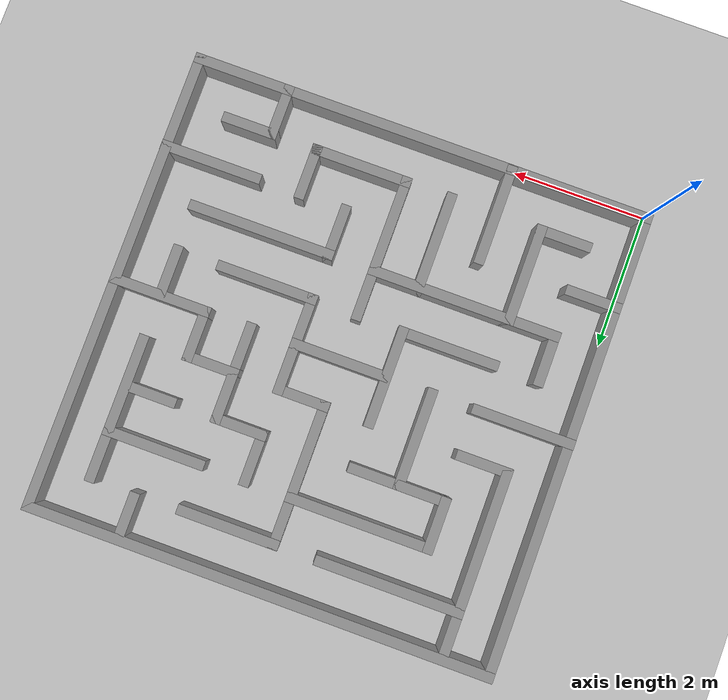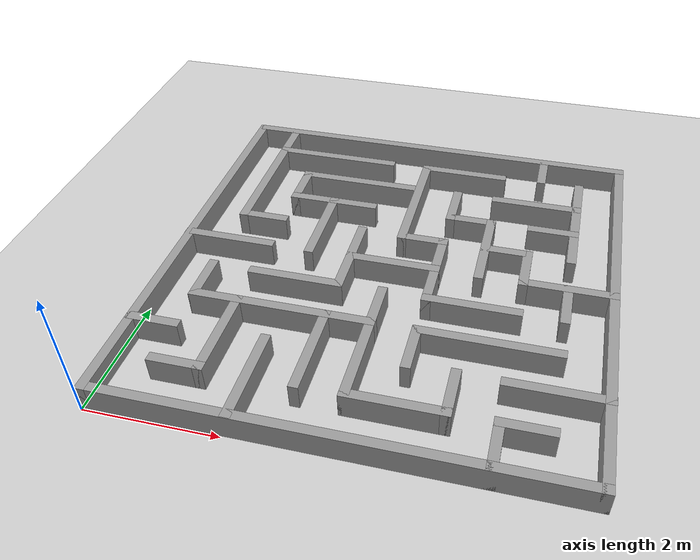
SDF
<sdf version="1.7">
 <world name="default">
  <scene><ambient>0.4 0.4 0.4 1</ambient><background>0.7 0.7 0.7 1</background><shadows>1</shadows></scene>
  <light name="sun" type="directional">
   <pose>0 0 10 0 -0 0</pose>
   <diffuse>0.8 0.8 0.8 1</diffuse>
   <specular>0.2 0.2 0.2 1</specular>
   <attenuation>
    <range>1000</range>
    <constant>0.9</constant>
    <linear>0.01</linear>
    <quadratic>0.001</quadratic>
   </attenuation>
   <direction>-0.5 0.1 -0.9</direction>
   <spot><inner_angle>0</inner_angle><outer_angle>0</outer_angle><falloff>0</falloff></spot>
  </light>
  <model name="ground_plane">
   <static>1</static>
   <link name="link">
    <collision name="collision">
     <geometry><plane><normal>0 0 1</normal><size>100 100</size></plane></geometry>
     <surface>
      <contact><collide_bitmask>65535</collide_bitmask></contact>
      <friction><ode><mu>100</mu><mu2>50</mu2></ode></friction>
     </surface>
    </collision>
    <visual name="visual">
     <cast_shadows>0</cast_shadows>
     <geometry><plane><normal>0 0 1</normal><size>100 100</size></plane></geometry>
     <material>
      <script><uri>file://media/materials/scripts/gazebo.material</uri><name>Gazebo/Grey</name></script>
     </material>
    </visual>
   </link>
  </model>
  <physics type="ode">
   <real_time_update_rate>1000</real_time_update_rate>
   <max_step_size>0.001</max_step_size>
   <real_time_factor>1</real_time_factor>
   <ode>
    <solver>
     <type>quick</type>
     <iters>150</iters>
     <precon_iters>0</precon_iters>
     <sor>1.4</sor>
     <use_dynamic_moi_rescaling>1</use_dynamic_moi_rescaling>
    </solver>
    <constraints>
     <cfm>1e-05</cfm>
     <erp>0.2</erp>
     <contact_max_correcting_vel>2000</contact_max_correcting_vel>
     <contact_surface_layer>0.01</contact_surface_layer>
    </constraints>
   </ode>
  </physics>
  <gravity>0 0 -9.8</gravity>
  <magnetic_field>6e-06 2.3e-05 -4.2e-05</magnetic_field>
  <atmosphere type="adiabatic"/>
  <spherical_coordinates>
   <surface_model>EARTH_WGS84</surface_model>
   <latitude_deg>0</latitude_deg>
   <longitude_deg>0</longitude_deg>
   <elevation>0</elevation>
   <heading_deg>0</heading_deg>
  </spherical_coordinates>
  <model name="Map_1">
   <link name="Wall_156">
    <pose>-3.425 0 0 0 0 -1.5708</pose>
    <inertial>
     <mass>1</mass>
     <inertia><ixx>1</ixx><ixy>0</ixy><ixz>0</ixz><iyy>1</iyy><iyz>0</iyz><izz>1</izz></inertia>
    </inertial>
    <visual name="Wall_156_Visual">
     <pose>0 0 0.2 0 -0 0</pose>
     <geometry><box><size>7 0.15 0.4</size></box></geometry>
     <material>
      <script><uri>file://media/materials/scripts/gazebo.material</uri><name>Gazebo/Grey</name></script>
      <ambient>1 1 1 1</ambient>
      <shader type="pixel"><normal_map>__default__</normal_map></shader>
      <diffuse>0.7 0.7 0.7 1</diffuse>
      <specular>0.01 0.01 0.01 1</specular>
      <emissive>0 0 0 1</emissive>
     </material>
     <meta><layer>0</layer></meta>
    </visual>
    <collision name="Wall_156_Collision">
     <pose>0 0 0.2 0 -0 0</pose>
     <geometry><box><size>7 0.15 0.4</size></box></geometry>
     <surface>
      <friction>
       <ode><mu>1</mu><mu2>1</mu2><fdir1>0 0 0</fdir1><slip1>0</slip1><slip2>0</slip2></ode>
       <torsional>
        <coefficient>1</coefficient>
        <patch_radius>0</patch_radius>
        <surface_radius>0</surface_radius>
        <use_patch_radius>1</use_patch_radius>
        <ode><slip>0</slip></ode>
       </torsional>
      </friction>
      <bounce><restitution_coefficient>0</restitution_coefficient><threshold>1e+06</threshold></bounce>
      <contact>
       <collide_without_contact>0</collide_without_contact>
       <collide_without_contact_bitmask>1</collide_without_contact_bitmask>
       <collide_bitmask>1</collide_bitmask>
       <ode>
        <soft_cfm>0</soft_cfm>
        <soft_erp>0.2</soft_erp>
        <kp>1e+13</kp>
        <kd>1</kd>
        <max_vel>0.01</max_vel>
        <min_depth>0</min_depth>
       </ode>
       <bullet>
        <split_impulse>1</split_impulse>
        <split_impulse_penetration_threshold>-0.01</split_impulse_penetration_threshold>
        <soft_cfm>0</soft_cfm>
        <soft_erp>0.2</soft_erp>
        <kp>1e+13</kp>
        <kd>1</kd>
       </bullet>
      </contact>
     </surface>
    </collision>
   </link>
   <link name="Wall_157">
    <pose>0 -3.425 0 0 -0 0</pose>
    <inertial>
     <mass>1</mass>
     <inertia><ixx>1</ixx><ixy>0</ixy><ixz>0</ixz><iyy>1</iyy><iyz>0</iyz><izz>1</izz></inertia>
    </inertial>
    <visual name="Wall_157_Visual">
     <pose>0 0 0.2 0 -0 0</pose>
     <geometry><box><size>7 0.15 0.4</size></box></geometry>
     <material>
      <script><uri>file://media/materials/scripts/gazebo.material</uri><name>Gazebo/Grey</name></script>
      <ambient>1 1 1 1</ambient>
      <shader type="pixel"><normal_map>__default__</normal_map></shader>
      <diffuse>0.7 0.7 0.7 1</diffuse>
      <specular>0.01 0.01 0.01 1</specular>
      <emissive>0 0 0 1</emissive>
     </material>
     <meta><layer>0</layer></meta>
    </visual>
    <collision name="Wall_157_Collision">
     <pose>0 0 0.2 0 -0 0</pose>
     <geometry><box><size>7 0.15 0.4</size></box></geometry>
     <surface>
      <friction>
       <ode><mu>1</mu><mu2>1</mu2><fdir1>0 0 0</fdir1><slip1>0</slip1><slip2>0</slip2></ode>
       <torsional>
        <coefficient>1</coefficient>
        <patch_radius>0</patch_radius>
        <surface_radius>0</surface_radius>
        <use_patch_radius>1</use_patch_radius>
        <ode><slip>0</slip></ode>
       </torsional>
      </friction>
      <bounce><restitution_coefficient>0</restitution_coefficient><threshold>1e+06</threshold></bounce>
      <contact>
       <collide_without_contact>0</collide_without_contact>
       <collide_without_contact_bitmask>1</collide_without_contact_bitmask>
       <collide_bitmask>1</collide_bitmask>
       <ode>
        <soft_cfm>0</soft_cfm>
        <soft_erp>0.2</soft_erp>
        <kp>1e+13</kp>
        <kd>1</kd>
        <max_vel>0.01</max_vel>
        <min_depth>0</min_depth>
       </ode>
       <bullet>
        <split_impulse>1</split_impulse>
        <split_impulse_penetration_threshold>-0.01</split_impulse_penetration_threshold>
        <soft_cfm>0</soft_cfm>
        <soft_erp>0.2</soft_erp>
        <kp>1e+13</kp>
        <kd>1</kd>
       </bullet>
      </contact>
     </surface>
    </collision>
   </link>
   <link name="Wall_158">
    <pose>3.425 0 0 0 -0 1.5708</pose>
    <inertial>
     <mass>1</mass>
     <inertia><ixx>1</ixx><ixy>0</ixy><ixz>0</ixz><iyy>1</iyy><iyz>0</iyz><izz>1</izz></inertia>
    </inertial>
    <visual name="Wall_158_Visual">
     <pose>0 0 0.2 0 -0 0</pose>
     <geometry><box><size>7 0.15 0.4</size></box></geometry>
     <material>
      <script><uri>file://media/materials/scripts/gazebo.material</uri><name>Gazebo/Grey</name></script>
      <ambient>1 1 1 1</ambient>
      <shader type="pixel"><normal_map>__default__</normal_map></shader>
      <diffuse>0.7 0.7 0.7 1</diffuse>
      <specular>0.01 0.01 0.01 1</specular>
      <emissive>0 0 0 1</emissive>
     </material>
     <meta><layer>0</layer></meta>
    </visual>
    <collision name="Wall_158_Collision">
     <pose>0 0 0.2 0 -0 0</pose>
     <geometry><box><size>7 0.15 0.4</size></box></geometry>
     <surface>
      <friction>
       <ode><mu>1</mu><mu2>1</mu2><fdir1>0 0 0</fdir1><slip1>0</slip1><slip2>0</slip2></ode>
       <torsional>
        <coefficient>1</coefficient>
        <patch_radius>0</patch_radius>
        <surface_radius>0</surface_radius>
        <use_patch_radius>1</use_patch_radius>
        <ode><slip>0</slip></ode>
       </torsional>
      </friction>
      <bounce><restitution_coefficient>0</restitution_coefficient><threshold>1e+06</threshold></bounce>
      <contact>
       <collide_without_contact>0</collide_without_contact>
       <collide_without_contact_bitmask>1</collide_without_contact_bitmask>
       <collide_bitmask>1</collide_bitmask>
       <ode>
        <soft_cfm>0</soft_cfm>
        <soft_erp>0.2</soft_erp>
        <kp>1e+13</kp>
        <kd>1</kd>
        <max_vel>0.01</max_vel>
        <min_depth>0</min_depth>
       </ode>
       <bullet>
        <split_impulse>1</split_impulse>
        <split_impulse_penetration_threshold>-0.01</split_impulse_penetration_threshold>
        <soft_cfm>0</soft_cfm>
        <soft_erp>0.2</soft_erp>
        <kp>1e+13</kp>
        <kd>1</kd>
       </bullet>
      </contact>
     </surface>
    </collision>
   </link>
   <link name="Wall_159">
    <pose>0 3.425 0 0 -0 3.14159</pose>
    <inertial>
     <mass>1</mass>
     <inertia><ixx>1</ixx><ixy>0</ixy><ixz>0</ixz><iyy>1</iyy><iyz>0</iyz><izz>1</izz></inertia>
    </inertial>
    <visual name="Wall_159_Visual">
     <pose>0 0 0.2 0 -0 0</pose>
     <geometry><box><size>7 0.15 0.4</size></box></geometry>
     <material>
      <script><uri>file://media/materials/scripts/gazebo.material</uri><name>Gazebo/Grey</name></script>
      <ambient>1 1 1 1</ambient>
      <shader type="pixel"><normal_map>__default__</normal_map></shader>
      <diffuse>0.7 0.7 0.7 1</diffuse>
      <specular>0.01 0.01 0.01 1</specular>
      <emissive>0 0 0 1</emissive>
     </material>
     <meta><layer>0</layer></meta>
    </visual>
    <collision name="Wall_159_Collision">
     <pose>0 0 0.2 0 -0 0</pose>
     <geometry><box><size>7 0.15 0.4</size></box></geometry>
     <surface>
      <friction>
       <ode><mu>1</mu><mu2>1</mu2><fdir1>0 0 0</fdir1><slip1>0</slip1><slip2>0</slip2></ode>
       <torsional>
        <coefficient>1</coefficient>
        <patch_radius>0</patch_radius>
        <surface_radius>0</surface_radius>
        <use_patch_radius>1</use_patch_radius>
        <ode><slip>0</slip></ode>
       </torsional>
      </friction>
      <bounce><restitution_coefficient>0</restitution_coefficient><threshold>1e+06</threshold></bounce>
      <contact>
       <collide_without_contact>0</collide_without_contact>
       <collide_without_contact_bitmask>1</collide_without_contact_bitmask>
       <collide_bitmask>1</collide_bitmask>
       <ode>
        <soft_cfm>0</soft_cfm>
        <soft_erp>0.2</soft_erp>
        <kp>1e+13</kp>
        <kd>1</kd>
        <max_vel>0.01</max_vel>
        <min_depth>0</min_depth>
       </ode>
       <bullet>
        <split_impulse>1</split_impulse>
        <split_impulse_penetration_threshold>-0.01</split_impulse_penetration_threshold>
        <soft_cfm>0</soft_cfm>
        <soft_erp>0.2</soft_erp>
        <kp>1e+13</kp>
        <kd>1</kd>
       </bullet>
      </contact>
     </surface>
    </collision>
   </link>
   <link name="Wall_185">
    <pose>-2.74 2.055 0 0 0 -1.5708</pose>
    <inertial>
     <mass>1</mass>
     <inertia><ixx>1</ixx><ixy>0</ixy><ixz>0</ixz><iyy>1</iyy><iyz>0</iyz><izz>1</izz></inertia>
    </inertial>
    <visual name="Wall_185_Visual">
     <pose>0 0 0.2 0 -0 0</pose>
     <geometry><box><size>2.89 0.15 0.4</size></box></geometry>
     <material>
      <script><uri>file://media/materials/scripts/gazebo.material</uri><name>Gazebo/Grey</name></script>
      <ambient>1 1 1 1</ambient>
      <shader type="pixel"><normal_map>__default__</normal_map></shader>
      <diffuse>0.7 0.7 0.7 1</diffuse>
      <specular>0.01 0.01 0.01 1</specular>
      <emissive>0 0 0 1</emissive>
     </material>
     <meta><layer>0</layer></meta>
    </visual>
    <collision name="Wall_185_Collision">
     <pose>0 0 0.2 0 -0 0</pose>
     <geometry><box><size>2.89 0.15 0.4</size></box></geometry>
     <surface>
      <friction>
       <ode><mu>1</mu><mu2>1</mu2><fdir1>0 0 0</fdir1><slip1>0</slip1><slip2>0</slip2></ode>
       <torsional>
        <coefficient>1</coefficient>
        <patch_radius>0</patch_radius>
        <surface_radius>0</surface_radius>
        <use_patch_radius>1</use_patch_radius>
        <ode><slip>0</slip></ode>
       </torsional>
      </friction>
      <bounce><restitution_coefficient>0</restitution_coefficient><threshold>1e+06</threshold></bounce>
      <contact>
       <collide_without_contact>0</collide_without_contact>
       <collide_without_contact_bitmask>1</collide_without_contact_bitmask>
       <collide_bitmask>1</collide_bitmask>
       <ode>
        <soft_cfm>0</soft_cfm>
        <soft_erp>0.2</soft_erp>
        <kp>1e+13</kp>
        <kd>1</kd>
        <max_vel>0.01</max_vel>
        <min_depth>0</min_depth>
       </ode>
       <bullet>
        <split_impulse>1</split_impulse>
        <split_impulse_penetration_threshold>-0.01</split_impulse_penetration_threshold>
        <soft_cfm>0</soft_cfm>
        <soft_erp>0.2</soft_erp>
        <kp>1e+13</kp>
        <kd>1</kd>
       </bullet>
      </contact>
     </surface>
    </collision>
   </link>
   <link name="Wall_188">
    <pose>-1.7125 2.74 0 0 -0 0</pose>
    <inertial>
     <mass>1</mass>
     <inertia><ixx>1</ixx><ixy>0</ixy><ixz>0</ixz><iyy>1</iyy><iyz>0</iyz><izz>1</izz></inertia>
    </inertial>
    <visual name="Wall_188_Visual">
     <pose>0 0 0.2 0 -0 0</pose>
     <geometry><box><size>2.205 0.15 0.4</size></box></geometry>
     <material>
      <script><uri>file://media/materials/scripts/gazebo.material</uri><name>Gazebo/Grey</name></script>
      <ambient>1 1 1 1</ambient>
      <shader type="pixel"><normal_map>__default__</normal_map></shader>
      <diffuse>0.7 0.7 0.7 1</diffuse>
      <specular>0.01 0.01 0.01 1</specular>
      <emissive>0 0 0 1</emissive>
     </material>
     <meta><layer>0</layer></meta>
    </visual>
    <collision name="Wall_188_Collision">
     <pose>0 0 0.2 0 -0 0</pose>
     <geometry><box><size>2.205 0.15 0.4</size></box></geometry>
     <surface>
      <friction>
       <ode><mu>1</mu><mu2>1</mu2><fdir1>0 0 0</fdir1><slip1>0</slip1><slip2>0</slip2></ode>
       <torsional>
        <coefficient>1</coefficient>
        <patch_radius>0</patch_radius>
        <surface_radius>0</surface_radius>
        <use_patch_radius>1</use_patch_radius>
        <ode><slip>0</slip></ode>
       </torsional>
      </friction>
      <bounce><restitution_coefficient>0</restitution_coefficient><threshold>1e+06</threshold></bounce>
      <contact>
       <collide_without_contact>0</collide_without_contact>
       <collide_without_contact_bitmask>1</collide_without_contact_bitmask>
       <collide_bitmask>1</collide_bitmask>
       <ode>
        <soft_cfm>0</soft_cfm>
        <soft_erp>0.2</soft_erp>
        <kp>1e+13</kp>
        <kd>1</kd>
        <max_vel>0.01</max_vel>
        <min_depth>0</min_depth>
       </ode>
       <bullet>
        <split_impulse>1</split_impulse>
        <split_impulse_penetration_threshold>-0.01</split_impulse_penetration_threshold>
        <soft_cfm>0</soft_cfm>
        <soft_erp>0.2</soft_erp>
        <kp>1e+13</kp>
        <kd>1</kd>
       </bullet>
      </contact>
     </surface>
    </collision>
   </link>
   <link name="Wall_191">
    <pose>0.685 2.74 0 0 -0 0</pose>
    <inertial>
     <mass>1</mass>
     <inertia><ixx>1</ixx><ixy>0</ixy><ixz>0</ixz><iyy>1</iyy><iyz>0</iyz><izz>1</izz></inertia>
    </inertial>
    <visual name="Wall_191_Visual">
     <pose>0 0 0.2 0 -0 0</pose>
     <geometry><box><size>1.52 0.15 0.4</size></box></geometry>
     <material>
      <script><uri>file://media/materials/scripts/gazebo.material</uri><name>Gazebo/Grey</name></script>
      <ambient>1 1 1 1</ambient>
      <shader type="pixel"><normal_map>__default__</normal_map></shader>
      <diffuse>0.7 0.7 0.7 1</diffuse>
      <specular>0.01 0.01 0.01 1</specular>
      <emissive>0 0 0 1</emissive>
     </material>
     <meta><layer>0</layer></meta>
    </visual>
    <collision name="Wall_191_Collision">
     <pose>0 0 0.2 0 -0 0</pose>
     <geometry><box><size>1.52 0.15 0.4</size></box></geometry>
     <surface>
      <friction>
       <ode><mu>1</mu><mu2>1</mu2><fdir1>0 0 0</fdir1><slip1>0</slip1><slip2>0</slip2></ode>
       <torsional>
        <coefficient>1</coefficient>
        <patch_radius>0</patch_radius>
        <surface_radius>0</surface_radius>
        <use_patch_radius>1</use_patch_radius>
        <ode><slip>0</slip></ode>
       </torsional>
      </friction>
      <bounce><restitution_coefficient>0</restitution_coefficient><threshold>1e+06</threshold></bounce>
      <contact>
       <collide_without_contact>0</collide_without_contact>
       <collide_without_contact_bitmask>1</collide_without_contact_bitmask>
       <collide_bitmask>1</collide_bitmask>
       <ode>
        <soft_cfm>0</soft_cfm>
        <soft_erp>0.2</soft_erp>
        <kp>1e+13</kp>
        <kd>1</kd>
        <max_vel>0.01</max_vel>
        <min_depth>0</min_depth>
       </ode>
       <bullet>
        <split_impulse>1</split_impulse>
        <split_impulse_penetration_threshold>-0.01</split_impulse_penetration_threshold>
        <soft_cfm>0</soft_cfm>
        <soft_erp>0.2</soft_erp>
        <kp>1e+13</kp>
        <kd>1</kd>
       </bullet>
      </contact>
     </surface>
    </collision>
   </link>
   <link name="Wall_194">
    <pose>2.055 2.055 0 0 -0 0</pose>
    <inertial>
     <mass>1</mass>
     <inertia><ixx>1</ixx><ixy>0</ixy><ixz>0</ixz><iyy>1</iyy><iyz>0</iyz><izz>1</izz></inertia>
    </inertial>
    <visual name="Wall_194_Visual">
     <pose>0 0 0.2 0 -0 0</pose>
     <geometry><box><size>1.52 0.15 0.4</size></box></geometry>
     <material>
      <script><uri>file://media/materials/scripts/gazebo.material</uri><name>Gazebo/Grey</name></script>
      <ambient>1 1 1 1</ambient>
      <shader type="pixel"><normal_map>__default__</normal_map></shader>
      <diffuse>0.7 0.7 0.7 1</diffuse>
      <specular>0.01 0.01 0.01 1</specular>
      <emissive>0 0 0 1</emissive>
     </material>
     <meta><layer>0</layer></meta>
    </visual>
    <collision name="Wall_194_Collision">
     <pose>0 0 0.2 0 -0 0</pose>
     <geometry><box><size>1.52 0.15 0.4</size></box></geometry>
     <surface>
      <friction>
       <ode><mu>1</mu><mu2>1</mu2><fdir1>0 0 0</fdir1><slip1>0</slip1><slip2>0</slip2></ode>
       <torsional>
        <coefficient>1</coefficient>
        <patch_radius>0</patch_radius>
        <surface_radius>0</surface_radius>
        <use_patch_radius>1</use_patch_radius>
        <ode><slip>0</slip></ode>
       </torsional>
      </friction>
      <bounce><restitution_coefficient>0</restitution_coefficient><threshold>1e+06</threshold></bounce>
      <contact>
       <collide_without_contact>0</collide_without_contact>
       <collide_without_contact_bitmask>1</collide_without_contact_bitmask>
       <collide_bitmask>1</collide_bitmask>
       <ode>
        <soft_cfm>0</soft_cfm>
        <soft_erp>0.2</soft_erp>
        <kp>1e+13</kp>
        <kd>1</kd>
        <max_vel>0.01</max_vel>
        <min_depth>0</min_depth>
       </ode>
       <bullet>
        <split_impulse>1</split_impulse>
        <split_impulse_penetration_threshold>-0.01</split_impulse_penetration_threshold>
        <soft_cfm>0</soft_cfm>
        <soft_erp>0.2</soft_erp>
        <kp>1e+13</kp>
        <kd>1</kd>
       </bullet>
      </contact>
     </surface>
    </collision>
   </link>
   <link name="Wall_196">
    <pose>2.74 1.7125 0 0 0 -1.5708</pose>
    <inertial>
     <mass>1</mass>
     <inertia><ixx>1</ixx><ixy>0</ixy><ixz>0</ixz><iyy>1</iyy><iyz>0</iyz><izz>1</izz></inertia>
    </inertial>
    <visual name="Wall_196_Visual">
     <pose>0 0 0.2 0 -0 0</pose>
     <geometry><box><size>2.205 0.15 0.4</size></box></geometry>
     <material>
      <script><uri>file://media/materials/scripts/gazebo.material</uri><name>Gazebo/Grey</name></script>
      <ambient>1 1 1 1</ambient>
      <shader type="pixel"><normal_map>__default__</normal_map></shader>
      <diffuse>0.7 0.7 0.7 1</diffuse>
      <specular>0.01 0.01 0.01 1</specular>
      <emissive>0 0 0 1</emissive>
     </material>
     <meta><layer>0</layer></meta>
    </visual>
    <collision name="Wall_196_Collision">
     <pose>0 0 0.2 0 -0 0</pose>
     <geometry><box><size>2.205 0.15 0.4</size></box></geometry>
     <surface>
      <friction>
       <ode><mu>1</mu><mu2>1</mu2><fdir1>0 0 0</fdir1><slip1>0</slip1><slip2>0</slip2></ode>
       <torsional>
        <coefficient>1</coefficient>
        <patch_radius>0</patch_radius>
        <surface_radius>0</surface_radius>
        <use_patch_radius>1</use_patch_radius>
        <ode><slip>0</slip></ode>
       </torsional>
      </friction>
      <bounce><restitution_coefficient>0</restitution_coefficient><threshold>1e+06</threshold></bounce>
      <contact>
       <collide_without_contact>0</collide_without_contact>
       <collide_without_contact_bitmask>1</collide_without_contact_bitmask>
       <collide_bitmask>1</collide_bitmask>
       <ode>
        <soft_cfm>0</soft_cfm>
        <soft_erp>0.2</soft_erp>
        <kp>1e+13</kp>
        <kd>1</kd>
        <max_vel>0.01</max_vel>
        <min_depth>0</min_depth>
       </ode>
       <bullet>
        <split_impulse>1</split_impulse>
        <split_impulse_penetration_threshold>-0.01</split_impulse_penetration_threshold>
        <soft_cfm>0</soft_cfm>
        <soft_erp>0.2</soft_erp>
        <kp>1e+13</kp>
        <kd>1</kd>
       </bullet>
      </contact>
     </surface>
    </collision>
   </link>
   <link name="Wall_198">
    <pose>2.07424 3.10446 0 0 0 -1.5708</pose>
    <inertial>
     <mass>1</mass>
     <inertia><ixx>1</ixx><ixy>0</ixy><ixz>0</ixz><iyy>1</iyy><iyz>0</iyz><izz>1</izz></inertia>
    </inertial>
    <visual name="Wall_198_Visual">
     <pose>0 0 0.2 0 -0 0</pose>
     <geometry><box><size>0.75 0.15 0.4</size></box></geometry>
     <material>
      <script><uri>file://media/materials/scripts/gazebo.material</uri><name>Gazebo/Grey</name></script>
      <ambient>1 1 1 1</ambient>
      <shader type="pixel"><normal_map>__default__</normal_map></shader>
      <diffuse>0.7 0.7 0.7 1</diffuse>
      <specular>0.01 0.01 0.01 1</specular>
      <emissive>0 0 0 1</emissive>
     </material>
     <meta><layer>0</layer></meta>
    </visual>
    <collision name="Wall_198_Collision">
     <pose>0 0 0.2 0 -0 0</pose>
     <geometry><box><size>0.75 0.15 0.4</size></box></geometry>
     <surface>
      <friction>
       <ode><mu>1</mu><mu2>1</mu2><fdir1>0 0 0</fdir1><slip1>0</slip1><slip2>0</slip2></ode>
       <torsional>
        <coefficient>1</coefficient>
        <patch_radius>0</patch_radius>
        <surface_radius>0</surface_radius>
        <use_patch_radius>1</use_patch_radius>
        <ode><slip>0</slip></ode>
       </torsional>
      </friction>
      <bounce><restitution_coefficient>0</restitution_coefficient><threshold>1e+06</threshold></bounce>
      <contact>
       <collide_without_contact>0</collide_without_contact>
       <collide_without_contact_bitmask>1</collide_without_contact_bitmask>
       <collide_bitmask>1</collide_bitmask>
       <ode>
        <soft_cfm>0</soft_cfm>
        <soft_erp>0.2</soft_erp>
        <kp>1e+13</kp>
        <kd>1</kd>
        <max_vel>0.01</max_vel>
        <min_depth>0</min_depth>
       </ode>
       <bullet>
        <split_impulse>1</split_impulse>
        <split_impulse_penetration_threshold>-0.01</split_impulse_penetration_threshold>
        <soft_cfm>0</soft_cfm>
        <soft_erp>0.2</soft_erp>
        <kp>1e+13</kp>
        <kd>1</kd>
       </bullet>
      </contact>
     </surface>
    </collision>
   </link>
   <link name="Wall_200">
    <pose>2.3975 1.37 0 0 -0 3.14159</pose>
    <inertial>
     <mass>1</mass>
     <inertia><ixx>1</ixx><ixy>0</ixy><ixz>0</ixz><iyy>1</iyy><iyz>0</iyz><izz>1</izz></inertia>
    </inertial>
    <visual name="Wall_200_Visual">
     <pose>0 0 0.2 0 -0 0</pose>
     <geometry><box><size>0.835 0.15 0.4</size></box></geometry>
     <material>
      <script><uri>file://media/materials/scripts/gazebo.material</uri><name>Gazebo/Grey</name></script>
      <ambient>1 1 1 1</ambient>
      <shader type="pixel"><normal_map>__default__</normal_map></shader>
      <diffuse>0.7 0.7 0.7 1</diffuse>
      <specular>0.01 0.01 0.01 1</specular>
      <emissive>0 0 0 1</emissive>
     </material>
     <meta><layer>0</layer></meta>
    </visual>
    <collision name="Wall_200_Collision">
     <pose>0 0 0.2 0 -0 0</pose>
     <geometry><box><size>0.835 0.15 0.4</size></box></geometry>
     <surface>
      <friction>
       <ode><mu>1</mu><mu2>1</mu2><fdir1>0 0 0</fdir1><slip1>0</slip1><slip2>0</slip2></ode>
       <torsional>
        <coefficient>1</coefficient>
        <patch_radius>0</patch_radius>
        <surface_radius>0</surface_radius>
        <use_patch_radius>1</use_patch_radius>
        <ode><slip>0</slip></ode>
       </torsional>
      </friction>
      <bounce><restitution_coefficient>0</restitution_coefficient><threshold>1e+06</threshold></bounce>
      <contact>
       <collide_without_contact>0</collide_without_contact>
       <collide_without_contact_bitmask>1</collide_without_contact_bitmask>
       <collide_bitmask>1</collide_bitmask>
       <ode>
        <soft_cfm>0</soft_cfm>
        <soft_erp>0.2</soft_erp>
        <kp>1e+13</kp>
        <kd>1</kd>
        <max_vel>0.01</max_vel>
        <min_depth>0</min_depth>
       </ode>
       <bullet>
        <split_impulse>1</split_impulse>
        <split_impulse_penetration_threshold>-0.01</split_impulse_penetration_threshold>
        <soft_cfm>0</soft_cfm>
        <soft_erp>0.2</soft_erp>
        <kp>1e+13</kp>
        <kd>1</kd>
       </bullet>
      </contact>
     </surface>
    </collision>
   </link>
   <link name="Wall_202">
    <pose>2.74 0 0 0 -0 3.14159</pose>
    <inertial>
     <mass>1</mass>
     <inertia><ixx>1</ixx><ixy>0</ixy><ixz>0</ixz><iyy>1</iyy><iyz>0</iyz><izz>1</izz></inertia>
    </inertial>
    <visual name="Wall_202_Visual">
     <pose>0 0 0.2 0 -0 0</pose>
     <geometry><box><size>1.52 0.15 0.4</size></box></geometry>
     <material>
      <script><uri>file://media/materials/scripts/gazebo.material</uri><name>Gazebo/Grey</name></script>
      <ambient>1 1 1 1</ambient>
      <shader type="pixel"><normal_map>__default__</normal_map></shader>
      <diffuse>0.7 0.7 0.7 1</diffuse>
      <specular>0.01 0.01 0.01 1</specular>
      <emissive>0 0 0 1</emissive>
     </material>
     <meta><layer>0</layer></meta>
    </visual>
    <collision name="Wall_202_Collision">
     <pose>0 0 0.2 0 -0 0</pose>
     <geometry><box><size>1.52 0.15 0.4</size></box></geometry>
     <surface>
      <friction>
       <ode><mu>1</mu><mu2>1</mu2><fdir1>0 0 0</fdir1><slip1>0</slip1><slip2>0</slip2></ode>
       <torsional>
        <coefficient>1</coefficient>
        <patch_radius>0</patch_radius>
        <surface_radius>0</surface_radius>
        <use_patch_radius>1</use_patch_radius>
        <ode><slip>0</slip></ode>
       </torsional>
      </friction>
      <bounce><restitution_coefficient>0</restitution_coefficient><threshold>1e+06</threshold></bounce>
      <contact>
       <collide_without_contact>0</collide_without_contact>
       <collide_without_contact_bitmask>1</collide_without_contact_bitmask>
       <collide_bitmask>1</collide_bitmask>
       <ode>
        <soft_cfm>0</soft_cfm>
        <soft_erp>0.2</soft_erp>
        <kp>1e+13</kp>
        <kd>1</kd>
        <max_vel>0.01</max_vel>
        <min_depth>0</min_depth>
       </ode>
       <bullet>
        <split_impulse>1</split_impulse>
        <split_impulse_penetration_threshold>-0.01</split_impulse_penetration_threshold>
        <soft_cfm>0</soft_cfm>
        <soft_erp>0.2</soft_erp>
        <kp>1e+13</kp>
        <kd>1</kd>
       </bullet>
      </contact>
     </surface>
    </collision>
   </link>
   <link name="Wall_204">
    <pose>2.055 0.3425 0 0 -0 1.5708</pose>
    <inertial>
     <mass>1</mass>
     <inertia><ixx>1</ixx><ixy>0</ixy><ixz>0</ixz><iyy>1</iyy><iyz>0</iyz><izz>1</izz></inertia>
    </inertial>
    <visual name="Wall_204_Visual">
     <pose>0 0 0.2 0 -0 0</pose>
     <geometry><box><size>0.835 0.15 0.4</size></box></geometry>
     <material>
      <script><uri>file://media/materials/scripts/gazebo.material</uri><name>Gazebo/Grey</name></script>
      <ambient>1 1 1 1</ambient>
      <shader type="pixel"><normal_map>__default__</normal_map></shader>
      <diffuse>0.7 0.7 0.7 1</diffuse>
      <specular>0.01 0.01 0.01 1</specular>
      <emissive>0 0 0 1</emissive>
     </material>
     <meta><layer>0</layer></meta>
    </visual>
    <collision name="Wall_204_Collision">
     <pose>0 0 0.2 0 -0 0</pose>
     <geometry><box><size>0.825 0.15 0.4</size></box></geometry>
     <surface>
      <friction>
       <ode><mu>1</mu><mu2>1</mu2><fdir1>0 0 0</fdir1><slip1>0</slip1><slip2>0</slip2></ode>
       <torsional>
        <coefficient>1</coefficient>
        <patch_radius>0</patch_radius>
        <surface_radius>0</surface_radius>
        <use_patch_radius>1</use_patch_radius>
        <ode><slip>0</slip></ode>
       </torsional>
      </friction>
      <bounce><restitution_coefficient>0</restitution_coefficient><threshold>1e+06</threshold></bounce>
      <contact>
       <collide_without_contact>0</collide_without_contact>
       <collide_without_contact_bitmask>1</collide_without_contact_bitmask>
       <collide_bitmask>1</collide_bitmask>
       <ode>
        <soft_cfm>0</soft_cfm>
        <soft_erp>0.2</soft_erp>
        <kp>1e+13</kp>
        <kd>1</kd>
        <max_vel>0.01</max_vel>
        <min_depth>0</min_depth>
       </ode>
       <bullet>
        <split_impulse>1</split_impulse>
        <split_impulse_penetration_threshold>-0.01</split_impulse_penetration_threshold>
        <soft_cfm>0</soft_cfm>
        <soft_erp>0.2</soft_erp>
        <kp>1e+13</kp>
        <kd>1</kd>
       </bullet>
      </contact>
     </surface>
    </collision>
   </link>
   <link name="Wall_206">
    <pose>1.37 0.685 0 0 -0 1.5708</pose>
    <inertial>
     <mass>1</mass>
     <inertia><ixx>1</ixx><ixy>0</ixy><ixz>0</ixz><iyy>1</iyy><iyz>0</iyz><izz>1</izz></inertia>
    </inertial>
    <visual name="Wall_206_Visual">
     <pose>0 0 0.2 0 -0 0</pose>
     <geometry><box><size>1.52 0.15 0.4</size></box></geometry>
     <material>
      <script><uri>file://media/materials/scripts/gazebo.material</uri><name>Gazebo/Grey</name></script>
      <ambient>1 1 1 1</ambient>
      <shader type="pixel"><normal_map>__default__</normal_map></shader>
      <diffuse>0.7 0.7 0.7 1</diffuse>
      <specular>0.01 0.01 0.01 1</specular>
      <emissive>0 0 0 1</emissive>
     </material>
     <meta><layer>0</layer></meta>
    </visual>
    <collision name="Wall_206_Collision">
     <pose>0 0 0.2 0 -0 0</pose>
     <geometry><box><size>1.52 0.15 0.4</size></box></geometry>
     <surface>
      <friction>
       <ode><mu>1</mu><mu2>1</mu2><fdir1>0 0 0</fdir1><slip1>0</slip1><slip2>0</slip2></ode>
       <torsional>
        <coefficient>1</coefficient>
        <patch_radius>0</patch_radius>
        <surface_radius>0</surface_radius>
        <use_patch_radius>1</use_patch_radius>
        <ode><slip>0</slip></ode>
       </torsional>
      </friction>
      <bounce><restitution_coefficient>0</restitution_coefficient><threshold>1e+06</threshold></bounce>
      <contact>
       <collide_without_contact>0</collide_without_contact>
       <collide_without_contact_bitmask>1</collide_without_contact_bitmask>
       <collide_bitmask>1</collide_bitmask>
       <ode>
        <soft_cfm>0</soft_cfm>
        <soft_erp>0.2</soft_erp>
        <kp>1e+13</kp>
        <kd>1</kd>
        <max_vel>0.01</max_vel>
        <min_depth>0</min_depth>
       </ode>
       <bullet>
        <split_impulse>1</split_impulse>
        <split_impulse_penetration_threshold>-0.01</split_impulse_penetration_threshold>
        <soft_cfm>0</soft_cfm>
        <soft_erp>0.2</soft_erp>
        <kp>1e+13</kp>
        <kd>1</kd>
       </bullet>
      </contact>
     </surface>
    </collision>
   </link>
   <link name="Wall_209">
    <pose>1.7125 0.685 0 0 -0 3.14159</pose>
    <inertial>
     <mass>1</mass>
     <inertia><ixx>1</ixx><ixy>0</ixy><ixz>0</ixz><iyy>1</iyy><iyz>0</iyz><izz>1</izz></inertia>
    </inertial>
    <visual name="Wall_209_Visual">
     <pose>0 0 0.2 0 -0 0</pose>
     <geometry><box><size>0.835 0.15 0.4</size></box></geometry>
     <material>
      <script><uri>file://media/materials/scripts/gazebo.material</uri><name>Gazebo/Grey</name></script>
      <ambient>1 1 1 1</ambient>
      <shader type="pixel"><normal_map>__default__</normal_map></shader>
      <diffuse>0.7 0.7 0.7 1</diffuse>
      <specular>0.01 0.01 0.01 1</specular>
      <emissive>0 0 0 1</emissive>
     </material>
     <meta><layer>0</layer></meta>
    </visual>
    <collision name="Wall_209_Collision">
     <pose>0 0 0.2 0 -0 0</pose>
     <geometry><box><size>0.835 0.15 0.4</size></box></geometry>
     <surface>
      <friction>
       <ode><mu>1</mu><mu2>1</mu2><fdir1>0 0 0</fdir1><slip1>0</slip1><slip2>0</slip2></ode>
       <torsional>
        <coefficient>1</coefficient>
        <patch_radius>0</patch_radius>
        <surface_radius>0</surface_radius>
        <use_patch_radius>1</use_patch_radius>
        <ode><slip>0</slip></ode>
       </torsional>
      </friction>
      <bounce><restitution_coefficient>0</restitution_coefficient><threshold>1e+06</threshold></bounce>
      <contact>
       <collide_without_contact>0</collide_without_contact>
       <collide_without_contact_bitmask>1</collide_without_contact_bitmask>
       <collide_bitmask>1</collide_bitmask>
       <ode>
        <soft_cfm>0</soft_cfm>
        <soft_erp>0.2</soft_erp>
        <kp>1e+13</kp>
        <kd>1</kd>
        <max_vel>0.01</max_vel>
        <min_depth>0</min_depth>
       </ode>
       <bullet>
        <split_impulse>1</split_impulse>
        <split_impulse_penetration_threshold>-0.01</split_impulse_penetration_threshold>
        <soft_cfm>0</soft_cfm>
        <soft_erp>0.2</soft_erp>
        <kp>1e+13</kp>
        <kd>1</kd>
       </bullet>
      </contact>
     </surface>
    </collision>
   </link>
   <link name="Wall_211">
    <pose>0 1.7125 0 0 0 -1.5708</pose>
    <inertial>
     <mass>1</mass>
     <inertia><ixx>1</ixx><ixy>0</ixy><ixz>0</ixz><iyy>1</iyy><iyz>0</iyz><izz>1</izz></inertia>
    </inertial>
    <visual name="Wall_211_Visual">
     <pose>0 0 0.2 0 -0 0</pose>
     <geometry><box><size>2.205 0.15 0.4</size></box></geometry>
     <material>
      <script><uri>file://media/materials/scripts/gazebo.material</uri><name>Gazebo/Grey</name></script>
      <ambient>1 1 1 1</ambient>
      <shader type="pixel"><normal_map>__default__</normal_map></shader>
      <diffuse>0.7 0.7 0.7 1</diffuse>
      <specular>0.01 0.01 0.01 1</specular>
      <emissive>0 0 0 1</emissive>
     </material>
     <meta><layer>0</layer></meta>
    </visual>
    <collision name="Wall_211_Collision">
     <pose>0 0 0.2 0 -0 0</pose>
     <geometry><box><size>2.205 0.15 0.4</size></box></geometry>
     <surface>
      <friction>
       <ode><mu>1</mu><mu2>1</mu2><fdir1>0 0 0</fdir1><slip1>0</slip1><slip2>0</slip2></ode>
       <torsional>
        <coefficient>1</coefficient>
        <patch_radius>0</patch_radius>
        <surface_radius>0</surface_radius>
        <use_patch_radius>1</use_patch_radius>
        <ode><slip>0</slip></ode>
       </torsional>
      </friction>
      <bounce><restitution_coefficient>0</restitution_coefficient><threshold>1e+06</threshold></bounce>
      <contact>
       <collide_without_contact>0</collide_without_contact>
       <collide_without_contact_bitmask>1</collide_without_contact_bitmask>
       <collide_bitmask>1</collide_bitmask>
       <ode>
        <soft_cfm>0</soft_cfm>
        <soft_erp>0.2</soft_erp>
        <kp>1e+13</kp>
        <kd>1</kd>
        <max_vel>0.01</max_vel>
        <min_depth>0</min_depth>
       </ode>
       <bullet>
        <split_impulse>1</split_impulse>
        <split_impulse_penetration_threshold>-0.01</split_impulse_penetration_threshold>
        <soft_cfm>0</soft_cfm>
        <soft_erp>0.2</soft_erp>
        <kp>1e+13</kp>
        <kd>1</kd>
       </bullet>
      </contact>
     </surface>
    </collision>
   </link>
   <link name="Wall_215">
    <pose>1.0275 1.37 0 0 -0 3.14159</pose>
    <inertial>
     <mass>1</mass>
     <inertia><ixx>1</ixx><ixy>0</ixy><ixz>0</ixz><iyy>1</iyy><iyz>0</iyz><izz>1</izz></inertia>
    </inertial>
    <visual name="Wall_215_Visual">
     <pose>0 0 0.2 0 -0 0</pose>
     <geometry><box><size>0.835 0.15 0.4</size></box></geometry>
     <material>
      <script><uri>file://media/materials/scripts/gazebo.material</uri><name>Gazebo/Grey</name></script>
      <ambient>1 1 1 1</ambient>
      <shader type="pixel"><normal_map>__default__</normal_map></shader>
      <diffuse>0.7 0.7 0.7 1</diffuse>
      <specular>0.01 0.01 0.01 1</specular>
      <emissive>0 0 0 1</emissive>
     </material>
     <meta><layer>0</layer></meta>
    </visual>
    <collision name="Wall_215_Collision">
     <pose>0 0 0.2 0 -0 0</pose>
     <geometry><box><size>0.835 0.15 0.4</size></box></geometry>
     <surface>
      <friction>
       <ode><mu>1</mu><mu2>1</mu2><fdir1>0 0 0</fdir1><slip1>0</slip1><slip2>0</slip2></ode>
       <torsional>
        <coefficient>1</coefficient>
        <patch_radius>0</patch_radius>
        <surface_radius>0</surface_radius>
        <use_patch_radius>1</use_patch_radius>
        <ode><slip>0</slip></ode>
       </torsional>
      </friction>
      <bounce><restitution_coefficient>0</restitution_coefficient><threshold>1e+06</threshold></bounce>
      <contact>
       <collide_without_contact>0</collide_without_contact>
       <collide_without_contact_bitmask>1</collide_without_contact_bitmask>
       <collide_bitmask>1</collide_bitmask>
       <ode>
        <soft_cfm>0</soft_cfm>
        <soft_erp>0.2</soft_erp>
        <kp>1e+13</kp>
        <kd>1</kd>
        <max_vel>0.01</max_vel>
        <min_depth>0</min_depth>
       </ode>
       <bullet>
        <split_impulse>1</split_impulse>
        <split_impulse_penetration_threshold>-0.01</split_impulse_penetration_threshold>
        <soft_cfm>0</soft_cfm>
        <soft_erp>0.2</soft_erp>
        <kp>1e+13</kp>
        <kd>1</kd>
       </bullet>
      </contact>
     </surface>
    </collision>
   </link>
   <link name="Wall_217">
    <pose>0.685 1.7125 0 0 -0 1.5708</pose>
    <inertial>
     <mass>1</mass>
     <inertia><ixx>1</ixx><ixy>0</ixy><ixz>0</ixz><iyy>1</iyy><iyz>0</iyz><izz>1</izz></inertia>
    </inertial>
    <visual name="Wall_217_Visual">
     <pose>0 0 0.2 0 -0 0</pose>
     <geometry><box><size>0.835 0.15 0.4</size></box></geometry>
     <material>
      <script><uri>file://media/materials/scripts/gazebo.material</uri><name>Gazebo/Grey</name></script>
      <ambient>1 1 1 1</ambient>
      <shader type="pixel"><normal_map>__default__</normal_map></shader>
      <diffuse>0.7 0.7 0.7 1</diffuse>
      <specular>0.01 0.01 0.01 1</specular>
      <emissive>0 0 0 1</emissive>
     </material>
     <meta><layer>0</layer></meta>
    </visual>
    <collision name="Wall_217_Collision">
     <pose>0 0 0.2 0 -0 0</pose>
     <geometry><box><size>0.835 0.15 0.4</size></box></geometry>
     <surface>
      <friction>
       <ode><mu>1</mu><mu2>1</mu2><fdir1>0 0 0</fdir1><slip1>0</slip1><slip2>0</slip2></ode>
       <torsional>
        <coefficient>1</coefficient>
        <patch_radius>0</patch_radius>
        <surface_radius>0</surface_radius>
        <use_patch_radius>1</use_patch_radius>
        <ode><slip>0</slip></ode>
       </torsional>
      </friction>
      <bounce><restitution_coefficient>0</restitution_coefficient><threshold>1e+06</threshold></bounce>
      <contact>
       <collide_without_contact>0</collide_without_contact>
       <collide_without_contact_bitmask>1</collide_without_contact_bitmask>
       <collide_bitmask>1</collide_bitmask>
       <ode>
        <soft_cfm>0</soft_cfm>
        <soft_erp>0.2</soft_erp>
        <kp>1e+13</kp>
        <kd>1</kd>
        <max_vel>0.01</max_vel>
        <min_depth>0</min_depth>
       </ode>
       <bullet>
        <split_impulse>1</split_impulse>
        <split_impulse_penetration_threshold>-0.01</split_impulse_penetration_threshold>
        <soft_cfm>0</soft_cfm>
        <soft_erp>0.2</soft_erp>
        <kp>1e+13</kp>
        <kd>1</kd>
       </bullet>
      </contact>
     </surface>
    </collision>
   </link>
   <link name="Wall_219">
    <pose>-1.0275 2.055 0 0 -0 3.14159</pose>
    <inertial>
     <mass>1</mass>
     <inertia><ixx>1</ixx><ixy>0</ixy><ixz>0</ixz><iyy>1</iyy><iyz>0</iyz><izz>1</izz></inertia>
    </inertial>
    <visual name="Wall_219_Visual">
     <pose>0 0 0.2 0 -0 0</pose>
     <geometry><box><size>2.205 0.15 0.4</size></box></geometry>
     <material>
      <script><uri>file://media/materials/scripts/gazebo.material</uri><name>Gazebo/Grey</name></script>
      <ambient>1 1 1 1</ambient>
      <shader type="pixel"><normal_map>__default__</normal_map></shader>
      <diffuse>0.7 0.7 0.7 1</diffuse>
      <specular>0.01 0.01 0.01 1</specular>
      <emissive>0 0 0 1</emissive>
     </material>
     <meta><layer>0</layer></meta>
    </visual>
    <collision name="Wall_219_Collision">
     <pose>0 0 0.2 0 -0 0</pose>
     <geometry><box><size>2.205 0.15 0.4</size></box></geometry>
     <surface>
      <friction>
       <ode><mu>1</mu><mu2>1</mu2><fdir1>0 0 0</fdir1><slip1>0</slip1><slip2>0</slip2></ode>
       <torsional>
        <coefficient>1</coefficient>
        <patch_radius>0</patch_radius>
        <surface_radius>0</surface_radius>
        <use_patch_radius>1</use_patch_radius>
        <ode><slip>0</slip></ode>
       </torsional>
      </friction>
      <bounce><restitution_coefficient>0</restitution_coefficient><threshold>1e+06</threshold></bounce>
      <contact>
       <collide_without_contact>0</collide_without_contact>
       <collide_without_contact_bitmask>1</collide_without_contact_bitmask>
       <collide_bitmask>1</collide_bitmask>
       <ode>
        <soft_cfm>0</soft_cfm>
        <soft_erp>0.2</soft_erp>
        <kp>1e+13</kp>
        <kd>1</kd>
        <max_vel>0.01</max_vel>
        <min_depth>0</min_depth>
       </ode>
       <bullet>
        <split_impulse>1</split_impulse>
        <split_impulse_penetration_threshold>-0.01</split_impulse_penetration_threshold>
        <soft_cfm>0</soft_cfm>
        <soft_erp>0.2</soft_erp>
        <kp>1e+13</kp>
        <kd>1</kd>
       </bullet>
      </contact>
     </surface>
    </collision>
   </link>
   <link name="Wall_221">
    <pose>-2.055 1.7125 0 0 0 -1.5708</pose>
    <inertial>
     <mass>1</mass>
     <inertia><ixx>1</ixx><ixy>0</ixy><ixz>0</ixz><iyy>1</iyy><iyz>0</iyz><izz>1</izz></inertia>
    </inertial>
    <visual name="Wall_221_Visual">
     <pose>0 0 0.2 0 -0 0</pose>
     <geometry><box><size>0.835 0.15 0.4</size></box></geometry>
     <material>
      <script><uri>file://media/materials/scripts/gazebo.material</uri><name>Gazebo/Grey</name></script>
      <ambient>1 1 1 1</ambient>
      <shader type="pixel"><normal_map>__default__</normal_map></shader>
      <diffuse>0.7 0.7 0.7 1</diffuse>
      <specular>0.01 0.01 0.01 1</specular>
      <emissive>0 0 0 1</emissive>
     </material>
     <meta><layer>0</layer></meta>
    </visual>
    <collision name="Wall_221_Collision">
     <pose>0 0 0.2 0 -0 0</pose>
     <geometry><box><size>0.835 0.15 0.4</size></box></geometry>
     <surface>
      <friction>
       <ode><mu>1</mu><mu2>1</mu2><fdir1>0 0 0</fdir1><slip1>0</slip1><slip2>0</slip2></ode>
       <torsional>
        <coefficient>1</coefficient>
        <patch_radius>0</patch_radius>
        <surface_radius>0</surface_radius>
        <use_patch_radius>1</use_patch_radius>
        <ode><slip>0</slip></ode>
       </torsional>
      </friction>
      <bounce><restitution_coefficient>0</restitution_coefficient><threshold>1e+06</threshold></bounce>
      <contact>
       <collide_without_contact>0</collide_without_contact>
       <collide_without_contact_bitmask>1</collide_without_contact_bitmask>
       <collide_bitmask>1</collide_bitmask>
       <ode>
        <soft_cfm>0</soft_cfm>
        <soft_erp>0.2</soft_erp>
        <kp>1e+13</kp>
        <kd>1</kd>
        <max_vel>0.01</max_vel>
        <min_depth>0</min_depth>
       </ode>
       <bullet>
        <split_impulse>1</split_impulse>
        <split_impulse_penetration_threshold>-0.01</split_impulse_penetration_threshold>
        <soft_cfm>0</soft_cfm>
        <soft_erp>0.2</soft_erp>
        <kp>1e+13</kp>
        <kd>1</kd>
       </bullet>
      </contact>
     </surface>
    </collision>
   </link>
   <link name="Wall_223">
    <pose>-1.37 1.37 0 0 -0 0</pose>
    <inertial>
     <mass>1</mass>
     <inertia><ixx>1</ixx><ixy>0</ixy><ixz>0</ixz><iyy>1</iyy><iyz>0</iyz><izz>1</izz></inertia>
    </inertial>
    <visual name="Wall_223_Visual">
     <pose>0 0 0.2 0 -0 0</pose>
     <geometry><box><size>1.52 0.15 0.4</size></box></geometry>
     <material>
      <script><uri>file://media/materials/scripts/gazebo.material</uri><name>Gazebo/Grey</name></script>
      <ambient>1 1 1 1</ambient>
      <shader type="pixel"><normal_map>__default__</normal_map></shader>
      <diffuse>0.7 0.7 0.7 1</diffuse>
      <specular>0.01 0.01 0.01 1</specular>
      <emissive>0 0 0 1</emissive>
     </material>
     <meta><layer>0</layer></meta>
    </visual>
    <collision name="Wall_223_Collision">
     <pose>0 0 0.2 0 -0 0</pose>
     <geometry><box><size>1.52 0.15 0.4</size></box></geometry>
     <surface>
      <friction>
       <ode><mu>1</mu><mu2>1</mu2><fdir1>0 0 0</fdir1><slip1>0</slip1><slip2>0</slip2></ode>
       <torsional>
        <coefficient>1</coefficient>
        <patch_radius>0</patch_radius>
        <surface_radius>0</surface_radius>
        <use_patch_radius>1</use_patch_radius>
        <ode><slip>0</slip></ode>
       </torsional>
      </friction>
      <bounce><restitution_coefficient>0</restitution_coefficient><threshold>1e+06</threshold></bounce>
      <contact>
       <collide_without_contact>0</collide_without_contact>
       <collide_without_contact_bitmask>1</collide_without_contact_bitmask>
       <collide_bitmask>1</collide_bitmask>
       <ode>
        <soft_cfm>0</soft_cfm>
        <soft_erp>0.2</soft_erp>
        <kp>1e+13</kp>
        <kd>1</kd>
        <max_vel>0.01</max_vel>
        <min_depth>0</min_depth>
       </ode>
       <bullet>
        <split_impulse>1</split_impulse>
        <split_impulse_penetration_threshold>-0.01</split_impulse_penetration_threshold>
        <soft_cfm>0</soft_cfm>
        <soft_erp>0.2</soft_erp>
        <kp>1e+13</kp>
        <kd>1</kd>
       </bullet>
      </contact>
     </surface>
    </collision>
   </link>
   <link name="Wall_225">
    <pose>-2.3975 0.685 0 0 -0 0</pose>
    <inertial>
     <mass>1</mass>
     <inertia><ixx>1</ixx><ixy>0</ixy><ixz>0</ixz><iyy>1</iyy><iyz>0</iyz><izz>1</izz></inertia>
    </inertial>
    <visual name="Wall_225_Visual">
     <pose>0 0 0.2 0 -0 0</pose>
     <geometry><box><size>0.835 0.15 0.4</size></box></geometry>
     <material>
      <script><uri>file://media/materials/scripts/gazebo.material</uri><name>Gazebo/Grey</name></script>
      <ambient>1 1 1 1</ambient>
      <shader type="pixel"><normal_map>__default__</normal_map></shader>
      <diffuse>0.7 0.7 0.7 1</diffuse>
      <specular>0.01 0.01 0.01 1</specular>
      <emissive>0 0 0 1</emissive>
     </material>
     <meta><layer>0</layer></meta>
    </visual>
    <collision name="Wall_225_Collision">
     <pose>0 0 0.2 0 -0 0</pose>
     <geometry><box><size>0.835 0.15 0.4</size></box></geometry>
     <surface>
      <friction>
       <ode><mu>1</mu><mu2>1</mu2><fdir1>0 0 0</fdir1><slip1>0</slip1><slip2>0</slip2></ode>
       <torsional>
        <coefficient>1</coefficient>
        <patch_radius>0</patch_radius>
        <surface_radius>0</surface_radius>
        <use_patch_radius>1</use_patch_radius>
        <ode><slip>0</slip></ode>
       </torsional>
      </friction>
      <bounce><restitution_coefficient>0</restitution_coefficient><threshold>1e+06</threshold></bounce>
      <contact>
       <collide_without_contact>0</collide_without_contact>
       <collide_without_contact_bitmask>1</collide_without_contact_bitmask>
       <collide_bitmask>1</collide_bitmask>
       <ode>
        <soft_cfm>0</soft_cfm>
        <soft_erp>0.2</soft_erp>
        <kp>1e+13</kp>
        <kd>1</kd>
        <max_vel>0.01</max_vel>
        <min_depth>0</min_depth>
       </ode>
       <bullet>
        <split_impulse>1</split_impulse>
        <split_impulse_penetration_threshold>-0.01</split_impulse_penetration_threshold>
        <soft_cfm>0</soft_cfm>
        <soft_erp>0.2</soft_erp>
        <kp>1e+13</kp>
        <kd>1</kd>
       </bullet>
      </contact>
     </surface>
    </collision>
   </link>
   <link name="Wall_227">
    <pose>-1.37 0.685 0 0 0 -1.5708</pose>
    <inertial>
     <mass>1</mass>
     <inertia><ixx>1</ixx><ixy>0</ixy><ixz>0</ixz><iyy>1</iyy><iyz>0</iyz><izz>1</izz></inertia>
    </inertial>
    <visual name="Wall_227_Visual">
     <pose>0 0 0.2 0 -0 0</pose>
     <geometry><box><size>1.52 0.15 0.4</size></box></geometry>
     <material>
      <script><uri>file://media/materials/scripts/gazebo.material</uri><name>Gazebo/Grey</name></script>
      <ambient>1 1 1 1</ambient>
      <shader type="pixel"><normal_map>__default__</normal_map></shader>
      <diffuse>0.7 0.7 0.7 1</diffuse>
      <specular>0.01 0.01 0.01 1</specular>
      <emissive>0 0 0 1</emissive>
     </material>
     <meta><layer>0</layer></meta>
    </visual>
    <collision name="Wall_227_Collision">
     <pose>0 0 0.2 0 -0 0</pose>
     <geometry><box><size>1.52 0.15 0.4</size></box></geometry>
     <surface>
      <friction>
       <ode><mu>1</mu><mu2>1</mu2><fdir1>0 0 0</fdir1><slip1>0</slip1><slip2>0</slip2></ode>
       <torsional>
        <coefficient>1</coefficient>
        <patch_radius>0</patch_radius>
        <surface_radius>0</surface_radius>
        <use_patch_radius>1</use_patch_radius>
        <ode><slip>0</slip></ode>
       </torsional>
      </friction>
      <bounce><restitution_coefficient>0</restitution_coefficient><threshold>1e+06</threshold></bounce>
      <contact>
       <collide_without_contact>0</collide_without_contact>
       <collide_without_contact_bitmask>1</collide_without_contact_bitmask>
       <collide_bitmask>1</collide_bitmask>
       <ode>
        <soft_cfm>0</soft_cfm>
        <soft_erp>0.2</soft_erp>
        <kp>1e+13</kp>
        <kd>1</kd>
        <max_vel>0.01</max_vel>
        <min_depth>0</min_depth>
       </ode>
       <bullet>
        <split_impulse>1</split_impulse>
        <split_impulse_penetration_threshold>-0.01</split_impulse_penetration_threshold>
        <soft_cfm>0</soft_cfm>
        <soft_erp>0.2</soft_erp>
        <kp>1e+13</kp>
        <kd>1</kd>
       </bullet>
      </contact>
     </surface>
    </collision>
   </link>
   <link name="Wall_229">
    <pose>-2.3975 0 0 0 -0 3.14159</pose>
    <inertial>
     <mass>1</mass>
     <inertia><ixx>1</ixx><ixy>0</ixy><ixz>0</ixz><iyy>1</iyy><iyz>0</iyz><izz>1</izz></inertia>
    </inertial>
    <visual name="Wall_229_Visual">
     <pose>0.342 0 0.2 0 -0 0</pose>
     <geometry><box><size>1.53 0.15 0.4</size></box></geometry>
     <material>
      <script><uri>file://media/materials/scripts/gazebo.material</uri><name>Gazebo/Grey</name></script>
      <ambient>1 1 1 1</ambient>
      <shader type="pixel"><normal_map>__default__</normal_map></shader>
      <diffuse>0.7 0.7 0.7 1</diffuse>
      <specular>0.01 0.01 0.01 1</specular>
      <emissive>0 0 0 1</emissive>
     </material>
     <meta><layer>0</layer></meta>
    </visual>
    <collision name="Wall_229_Collision">
     <pose>0.342 0 0.2 0 -0 0</pose>
     <geometry><box><size>1.53 0.15 0.4</size></box></geometry>
     <surface>
      <friction>
       <ode><mu>1</mu><mu2>1</mu2><fdir1>0 0 0</fdir1><slip1>0</slip1><slip2>0</slip2></ode>
       <torsional>
        <coefficient>1</coefficient>
        <patch_radius>0</patch_radius>
        <surface_radius>0</surface_radius>
        <use_patch_radius>1</use_patch_radius>
        <ode><slip>0</slip></ode>
       </torsional>
      </friction>
      <bounce><restitution_coefficient>0</restitution_coefficient><threshold>1e+06</threshold></bounce>
      <contact>
       <collide_without_contact>0</collide_without_contact>
       <collide_without_contact_bitmask>1</collide_without_contact_bitmask>
       <collide_bitmask>1</collide_bitmask>
       <ode>
        <soft_cfm>0</soft_cfm>
        <soft_erp>0.2</soft_erp>
        <kp>1e+13</kp>
        <kd>1</kd>
        <max_vel>0.01</max_vel>
        <min_depth>0</min_depth>
       </ode>
       <bullet>
        <split_impulse>1</split_impulse>
        <split_impulse_penetration_threshold>-0.01</split_impulse_penetration_threshold>
        <soft_cfm>0</soft_cfm>
        <soft_erp>0.2</soft_erp>
        <kp>1e+13</kp>
        <kd>1</kd>
       </bullet>
      </contact>
     </surface>
    </collision>
   </link>
   <link name="Wall_231">
    <pose>0.3425 0.685 0 0 -0 0</pose>
    <inertial>
     <mass>1</mass>
     <inertia><ixx>1</ixx><ixy>0</ixy><ixz>0</ixz><iyy>1</iyy><iyz>0</iyz><izz>1</izz></inertia>
    </inertial>
    <visual name="Wall_231_Visual">
     <pose>0 0 0.2 0 -0 0</pose>
     <geometry><box><size>0.835 0.15 0.4</size></box></geometry>
     <material>
      <script><uri>file://media/materials/scripts/gazebo.material</uri><name>Gazebo/Grey</name></script>
      <ambient>1 1 1 1</ambient>
      <shader type="pixel"><normal_map>__default__</normal_map></shader>
      <diffuse>0.7 0.7 0.7 1</diffuse>
      <specular>0.01 0.01 0.01 1</specular>
      <emissive>0 0 0 1</emissive>
     </material>
     <meta><layer>0</layer></meta>
    </visual>
    <collision name="Wall_231_Collision">
     <pose>0 0 0.2 0 -0 0</pose>
     <geometry><box><size>0.835 0.15 0.4</size></box></geometry>
     <surface>
      <friction>
       <ode><mu>1</mu><mu2>1</mu2><fdir1>0 0 0</fdir1><slip1>0</slip1><slip2>0</slip2></ode>
       <torsional>
        <coefficient>1</coefficient>
        <patch_radius>0</patch_radius>
        <surface_radius>0</surface_radius>
        <use_patch_radius>1</use_patch_radius>
        <ode><slip>0</slip></ode>
       </torsional>
      </friction>
      <bounce><restitution_coefficient>0</restitution_coefficient><threshold>1e+06</threshold></bounce>
      <contact>
       <collide_without_contact>0</collide_without_contact>
       <collide_without_contact_bitmask>1</collide_without_contact_bitmask>
       <collide_bitmask>1</collide_bitmask>
       <ode>
        <soft_cfm>0</soft_cfm>
        <soft_erp>0.2</soft_erp>
        <kp>1e+13</kp>
        <kd>1</kd>
        <max_vel>0.01</max_vel>
        <min_depth>0</min_depth>
       </ode>
       <bullet>
        <split_impulse>1</split_impulse>
        <split_impulse_penetration_threshold>-0.01</split_impulse_penetration_threshold>
        <soft_cfm>0</soft_cfm>
        <soft_erp>0.2</soft_erp>
        <kp>1e+13</kp>
        <kd>1</kd>
       </bullet>
      </contact>
     </surface>
    </collision>
   </link>
   <link name="Wall_233">
    <pose>0.685 0 0 0 0 -1.5708</pose>
    <inertial>
     <mass>1</mass>
     <inertia><ixx>1</ixx><ixy>0</ixy><ixz>0</ixz><iyy>1</iyy><iyz>0</iyz><izz>1</izz></inertia>
    </inertial>
    <visual name="Wall_233_Visual">
     <pose>0 0 0.2 0 -0 0</pose>
     <geometry><box><size>1.52 0.15 0.4</size></box></geometry>
     <material>
      <script><uri>file://media/materials/scripts/gazebo.material</uri><name>Gazebo/Grey</name></script>
      <ambient>1 1 1 1</ambient>
      <shader type="pixel"><normal_map>__default__</normal_map></shader>
      <diffuse>0.7 0.7 0.7 1</diffuse>
      <specular>0.01 0.01 0.01 1</specular>
      <emissive>0 0 0 1</emissive>
     </material>
     <meta><layer>0</layer></meta>
    </visual>
    <collision name="Wall_233_Collision">
     <pose>0 0 0.2 0 -0 0</pose>
     <geometry><box><size>1.52 0.15 0.4</size></box></geometry>
     <surface>
      <friction>
       <ode><mu>1</mu><mu2>1</mu2><fdir1>0 0 0</fdir1><slip1>0</slip1><slip2>0</slip2></ode>
       <torsional>
        <coefficient>1</coefficient>
        <patch_radius>0</patch_radius>
        <surface_radius>0</surface_radius>
        <use_patch_radius>1</use_patch_radius>
        <ode><slip>0</slip></ode>
       </torsional>
      </friction>
      <bounce><restitution_coefficient>0</restitution_coefficient><threshold>1e+06</threshold></bounce>
      <contact>
       <collide_without_contact>0</collide_without_contact>
       <collide_without_contact_bitmask>1</collide_without_contact_bitmask>
       <collide_bitmask>1</collide_bitmask>
       <ode>
        <soft_cfm>0</soft_cfm>
        <soft_erp>0.2</soft_erp>
        <kp>1e+13</kp>
        <kd>1</kd>
        <max_vel>0.01</max_vel>
        <min_depth>0</min_depth>
       </ode>
       <bullet>
        <split_impulse>1</split_impulse>
        <split_impulse_penetration_threshold>-0.01</split_impulse_penetration_threshold>
        <soft_cfm>0</soft_cfm>
        <soft_erp>0.2</soft_erp>
        <kp>1e+13</kp>
        <kd>1</kd>
       </bullet>
      </contact>
     </surface>
    </collision>
   </link>
   <link name="Wall_235">
    <pose>-1.37 -0.685 0 0 -0 0</pose>
    <inertial>
     <mass>1</mass>
     <inertia><ixx>1</ixx><ixy>0</ixy><ixz>0</ixz><iyy>1</iyy><iyz>0</iyz><izz>1</izz></inertia>
    </inertial>
    <visual name="Wall_235_Visual">
     <pose>0 0 0.2 0 -0 0</pose>
     <geometry><box><size>1.52 0.15 0.4</size></box></geometry>
     <material>
      <script><uri>file://media/materials/scripts/gazebo.material</uri><name>Gazebo/Grey</name></script>
      <ambient>1 1 1 1</ambient>
      <shader type="pixel"><normal_map>__default__</normal_map></shader>
      <diffuse>0.7 0.7 0.7 1</diffuse>
      <specular>0.01 0.01 0.01 1</specular>
      <emissive>0 0 0 1</emissive>
     </material>
     <meta><layer>0</layer></meta>
    </visual>
    <collision name="Wall_235_Collision">
     <pose>0 0 0.2 0 -0 0</pose>
     <geometry><box><size>1.52 0.15 0.4</size></box></geometry>
     <surface>
      <friction>
       <ode><mu>1</mu><mu2>1</mu2><fdir1>0 0 0</fdir1><slip1>0</slip1><slip2>0</slip2></ode>
       <torsional>
        <coefficient>1</coefficient>
        <patch_radius>0</patch_radius>
        <surface_radius>0</surface_radius>
        <use_patch_radius>1</use_patch_radius>
        <ode><slip>0</slip></ode>
       </torsional>
      </friction>
      <bounce><restitution_coefficient>0</restitution_coefficient><threshold>1e+06</threshold></bounce>
      <contact>
       <collide_without_contact>0</collide_without_contact>
       <collide_without_contact_bitmask>1</collide_without_contact_bitmask>
       <collide_bitmask>1</collide_bitmask>
       <ode>
        <soft_cfm>0</soft_cfm>
        <soft_erp>0.2</soft_erp>
        <kp>1e+13</kp>
        <kd>1</kd>
        <max_vel>0.01</max_vel>
        <min_depth>0</min_depth>
       </ode>
       <bullet>
        <split_impulse>1</split_impulse>
        <split_impulse_penetration_threshold>-0.01</split_impulse_penetration_threshold>
        <soft_cfm>0</soft_cfm>
        <soft_erp>0.2</soft_erp>
        <kp>1e+13</kp>
        <kd>1</kd>
       </bullet>
      </contact>
     </surface>
    </collision>
   </link>
   <link name="Wall_237">
    <pose>-0.685 0 0 0 -0 1.5708</pose>
    <inertial>
     <mass>1</mass>
     <inertia><ixx>1</ixx><ixy>0</ixy><ixz>0</ixz><iyy>1</iyy><iyz>0</iyz><izz>1</izz></inertia>
    </inertial>
    <visual name="Wall_237_Visual">
     <pose>0 0 0.2 0 -0 0</pose>
     <geometry><box><size>1.52 0.15 0.4</size></box></geometry>
     <material>
      <script><uri>file://media/materials/scripts/gazebo.material</uri><name>Gazebo/Grey</name></script>
      <ambient>1 1 1 1</ambient>
      <shader type="pixel"><normal_map>__default__</normal_map></shader>
      <diffuse>0.7 0.7 0.7 1</diffuse>
      <specular>0.01 0.01 0.01 1</specular>
      <emissive>0 0 0 1</emissive>
     </material>
     <meta><layer>0</layer></meta>
    </visual>
    <collision name="Wall_237_Collision">
     <pose>0 0 0.2 0 -0 0</pose>
     <geometry><box><size>1.52 0.15 0.4</size></box></geometry>
     <surface>
      <friction>
       <ode><mu>1</mu><mu2>1</mu2><fdir1>0 0 0</fdir1><slip1>0</slip1><slip2>0</slip2></ode>
       <torsional>
        <coefficient>1</coefficient>
        <patch_radius>0</patch_radius>
        <surface_radius>0</surface_radius>
        <use_patch_radius>1</use_patch_radius>
        <ode><slip>0</slip></ode>
       </torsional>
      </friction>
      <bounce><restitution_coefficient>0</restitution_coefficient><threshold>1e+06</threshold></bounce>
      <contact>
       <collide_without_contact>0</collide_without_contact>
       <collide_without_contact_bitmask>1</collide_without_contact_bitmask>
       <collide_bitmask>1</collide_bitmask>
       <ode>
        <soft_cfm>0</soft_cfm>
        <soft_erp>0.2</soft_erp>
        <kp>1e+13</kp>
        <kd>1</kd>
        <max_vel>0.01</max_vel>
        <min_depth>0</min_depth>
       </ode>
       <bullet>
        <split_impulse>1</split_impulse>
        <split_impulse_penetration_threshold>-0.01</split_impulse_penetration_threshold>
        <soft_cfm>0</soft_cfm>
        <soft_erp>0.2</soft_erp>
        <kp>1e+13</kp>
        <kd>1</kd>
       </bullet>
      </contact>
     </surface>
    </collision>
   </link>
   <link name="Wall_239">
    <inertial>
     <mass>1</mass>
     <inertia><ixx>1</ixx><ixy>0</ixy><ixz>0</ixz><iyy>1</iyy><iyz>0</iyz><izz>1</izz></inertia>
    </inertial>
    <visual name="Wall_239_Visual">
     <pose>0 0 0.2 0 -0 0</pose>
     <geometry><box><size>1.52 0.15 0.4</size></box></geometry>
     <material>
      <script><uri>file://media/materials/scripts/gazebo.material</uri><name>Gazebo/Grey</name></script>
      <ambient>1 1 1 1</ambient>
      <shader type="pixel"><normal_map>__default__</normal_map></shader>
      <diffuse>0.7 0.7 0.7 1</diffuse>
      <specular>0.01 0.01 0.01 1</specular>
      <emissive>0 0 0 1</emissive>
     </material>
     <meta><layer>0</layer></meta>
    </visual>
    <collision name="Wall_239_Collision">
     <pose>0 0 0.2 0 -0 0</pose>
     <geometry><box><size>1.52 0.15 0.4</size></box></geometry>
     <surface>
      <friction>
       <ode><mu>1</mu><mu2>1</mu2><fdir1>0 0 0</fdir1><slip1>0</slip1><slip2>0</slip2></ode>
       <torsional>
        <coefficient>1</coefficient>
        <patch_radius>0</patch_radius>
        <surface_radius>0</surface_radius>
        <use_patch_radius>1</use_patch_radius>
        <ode><slip>0</slip></ode>
       </torsional>
      </friction>
      <bounce><restitution_coefficient>0</restitution_coefficient><threshold>1e+06</threshold></bounce>
      <contact>
       <collide_without_contact>0</collide_without_contact>
       <collide_without_contact_bitmask>1</collide_without_contact_bitmask>
       <collide_bitmask>1</collide_bitmask>
       <ode>
        <soft_cfm>0</soft_cfm>
        <soft_erp>0.2</soft_erp>
        <kp>1e+13</kp>
        <kd>1</kd>
        <max_vel>0.01</max_vel>
        <min_depth>0</min_depth>
       </ode>
       <bullet>
        <split_impulse>1</split_impulse>
        <split_impulse_penetration_threshold>-0.01</split_impulse_penetration_threshold>
        <soft_cfm>0</soft_cfm>
        <soft_erp>0.2</soft_erp>
        <kp>1e+13</kp>
        <kd>1</kd>
       </bullet>
      </contact>
     </surface>
    </collision>
   </link>
   <link name="Wall_241">
    <pose>1.37 -0.685 0 0 -0 0</pose>
    <inertial>
     <mass>1</mass>
     <inertia><ixx>1</ixx><ixy>0</ixy><ixz>0</ixz><iyy>1</iyy><iyz>0</iyz><izz>1</izz></inertia>
    </inertial>
    <visual name="Wall_241_Visual">
     <pose>0 0 0.2 0 -0 0</pose>
     <geometry><box><size>1.52 0.15 0.4</size></box></geometry>
     <material>
      <script><uri>file://media/materials/scripts/gazebo.material</uri><name>Gazebo/Grey</name></script>
      <ambient>1 1 1 1</ambient>
      <shader type="pixel"><normal_map>__default__</normal_map></shader>
      <diffuse>0.7 0.7 0.7 1</diffuse>
      <specular>0.01 0.01 0.01 1</specular>
      <emissive>0 0 0 1</emissive>
     </material>
     <meta><layer>0</layer></meta>
    </visual>
    <collision name="Wall_241_Collision">
     <pose>0 0 0.2 0 -0 0</pose>
     <geometry><box><size>1.52 0.15 0.4</size></box></geometry>
     <surface>
      <friction>
       <ode><mu>1</mu><mu2>1</mu2><fdir1>0 0 0</fdir1><slip1>0</slip1><slip2>0</slip2></ode>
       <torsional>
        <coefficient>1</coefficient>
        <patch_radius>0</patch_radius>
        <surface_radius>0</surface_radius>
        <use_patch_radius>1</use_patch_radius>
        <ode><slip>0</slip></ode>
       </torsional>
      </friction>
      <bounce><restitution_coefficient>0</restitution_coefficient><threshold>1e+06</threshold></bounce>
      <contact>
       <collide_without_contact>0</collide_without_contact>
       <collide_without_contact_bitmask>1</collide_without_contact_bitmask>
       <collide_bitmask>1</collide_bitmask>
       <ode>
        <soft_cfm>0</soft_cfm>
        <soft_erp>0.2</soft_erp>
        <kp>1e+13</kp>
        <kd>1</kd>
        <max_vel>0.01</max_vel>
        <min_depth>0</min_depth>
       </ode>
       <bullet>
        <split_impulse>1</split_impulse>
        <split_impulse_penetration_threshold>-0.01</split_impulse_penetration_threshold>
        <soft_cfm>0</soft_cfm>
        <soft_erp>0.2</soft_erp>
        <kp>1e+13</kp>
        <kd>1</kd>
       </bullet>
      </contact>
     </surface>
    </collision>
   </link>
   <link name="Wall_243">
    <pose>2.74 -0.3425 0 0 0 -1.5708</pose>
    <inertial>
     <mass>1</mass>
     <inertia><ixx>1</ixx><ixy>0</ixy><ixz>0</ixz><iyy>1</iyy><iyz>0</iyz><izz>1</izz></inertia>
    </inertial>
    <visual name="Wall_243_Visual">
     <pose>0 0 0.2 0 -0 0</pose>
     <geometry><box><size>0.835 0.15 0.4</size></box></geometry>
     <material>
      <script><uri>file://media/materials/scripts/gazebo.material</uri><name>Gazebo/Grey</name></script>
      <ambient>1 1 1 1</ambient>
      <shader type="pixel"><normal_map>__default__</normal_map></shader>
      <diffuse>0.7 0.7 0.7 1</diffuse>
      <specular>0.01 0.01 0.01 1</specular>
      <emissive>0 0 0 1</emissive>
     </material>
     <meta><layer>0</layer></meta>
    </visual>
    <collision name="Wall_243_Collision">
     <pose>0 0 0.2 0 -0 0</pose>
     <geometry><box><size>0.835 0.15 0.4</size></box></geometry>
     <surface>
      <friction>
       <ode><mu>1</mu><mu2>1</mu2><fdir1>0 0 0</fdir1><slip1>0</slip1><slip2>0</slip2></ode>
       <torsional>
        <coefficient>1</coefficient>
        <patch_radius>0</patch_radius>
        <surface_radius>0</surface_radius>
        <use_patch_radius>1</use_patch_radius>
        <ode><slip>0</slip></ode>
       </torsional>
      </friction>
      <bounce><restitution_coefficient>0</restitution_coefficient><threshold>1e+06</threshold></bounce>
      <contact>
       <collide_without_contact>0</collide_without_contact>
       <collide_without_contact_bitmask>1</collide_without_contact_bitmask>
       <collide_bitmask>1</collide_bitmask>
       <ode>
        <soft_cfm>0</soft_cfm>
        <soft_erp>0.2</soft_erp>
        <kp>1e+13</kp>
        <kd>1</kd>
        <max_vel>0.01</max_vel>
        <min_depth>0</min_depth>
       </ode>
       <bullet>
        <split_impulse>1</split_impulse>
        <split_impulse_penetration_threshold>-0.01</split_impulse_penetration_threshold>
        <soft_cfm>0</soft_cfm>
        <soft_erp>0.2</soft_erp>
        <kp>1e+13</kp>
        <kd>1</kd>
       </bullet>
      </contact>
     </surface>
    </collision>
   </link>
   <link name="Wall_245">
    <pose>-1.37 -1.37 0 0 -0 0</pose>
    <inertial>
     <mass>1</mass>
     <inertia><ixx>1</ixx><ixy>0</ixy><ixz>0</ixz><iyy>1</iyy><iyz>0</iyz><izz>1</izz></inertia>
    </inertial>
    <visual name="Wall_245_Visual">
     <pose>0 0 0.2 0 -0 0</pose>
     <geometry><box><size>2.89 0.15 0.4</size></box></geometry>
     <material>
      <script><uri>file://media/materials/scripts/gazebo.material</uri><name>Gazebo/Grey</name></script>
      <ambient>1 1 1 1</ambient>
      <shader type="pixel"><normal_map>__default__</normal_map></shader>
      <diffuse>0.7 0.7 0.7 1</diffuse>
      <specular>0.01 0.01 0.01 1</specular>
      <emissive>0 0 0 1</emissive>
     </material>
     <meta><layer>0</layer></meta>
    </visual>
    <collision name="Wall_245_Collision">
     <pose>0 0 0.2 0 -0 0</pose>
     <geometry><box><size>2.89 0.15 0.4</size></box></geometry>
     <surface>
      <friction>
       <ode><mu>1</mu><mu2>1</mu2><fdir1>0 0 0</fdir1><slip1>0</slip1><slip2>0</slip2></ode>
       <torsional>
        <coefficient>1</coefficient>
        <patch_radius>0</patch_radius>
        <surface_radius>0</surface_radius>
        <use_patch_radius>1</use_patch_radius>
        <ode><slip>0</slip></ode>
       </torsional>
      </friction>
      <bounce><restitution_coefficient>0</restitution_coefficient><threshold>1e+06</threshold></bounce>
      <contact>
       <collide_without_contact>0</collide_without_contact>
       <collide_without_contact_bitmask>1</collide_without_contact_bitmask>
       <collide_bitmask>1</collide_bitmask>
       <ode>
        <soft_cfm>0</soft_cfm>
        <soft_erp>0.2</soft_erp>
        <kp>1e+13</kp>
        <kd>1</kd>
        <max_vel>0.01</max_vel>
        <min_depth>0</min_depth>
       </ode>
       <bullet>
        <split_impulse>1</split_impulse>
        <split_impulse_penetration_threshold>-0.01</split_impulse_penetration_threshold>
        <soft_cfm>0</soft_cfm>
        <soft_erp>0.2</soft_erp>
        <kp>1e+13</kp>
        <kd>1</kd>
       </bullet>
      </contact>
     </surface>
    </collision>
   </link>
   <link name="Wall_247">
    <pose>-2.74 -1.0275 0 0 -0 1.5708</pose>
    <inertial>
     <mass>1</mass>
     <inertia><ixx>1</ixx><ixy>0</ixy><ixz>0</ixz><iyy>1</iyy><iyz>0</iyz><izz>1</izz></inertia>
    </inertial>
    <visual name="Wall_247_Visual">
     <pose>0 0 0.2 0 -0 0</pose>
     <geometry><box><size>0.835 0.15 0.4</size></box></geometry>
     <material>
      <script><uri>file://media/materials/scripts/gazebo.material</uri><name>Gazebo/Grey</name></script>
      <ambient>1 1 1 1</ambient>
      <shader type="pixel"><normal_map>__default__</normal_map></shader>
      <diffuse>0.7 0.7 0.7 1</diffuse>
      <specular>0.01 0.01 0.01 1</specular>
      <emissive>0 0 0 1</emissive>
     </material>
     <meta><layer>0</layer></meta>
    </visual>
    <collision name="Wall_247_Collision">
     <pose>0 0 0.2 0 -0 0</pose>
     <geometry><box><size>0.835 0.15 0.4</size></box></geometry>
     <surface>
      <friction>
       <ode><mu>1</mu><mu2>1</mu2><fdir1>0 0 0</fdir1><slip1>0</slip1><slip2>0</slip2></ode>
       <torsional>
        <coefficient>1</coefficient>
        <patch_radius>0</patch_radius>
        <surface_radius>0</surface_radius>
        <use_patch_radius>1</use_patch_radius>
        <ode><slip>0</slip></ode>
       </torsional>
      </friction>
      <bounce><restitution_coefficient>0</restitution_coefficient><threshold>1e+06</threshold></bounce>
      <contact>
       <collide_without_contact>0</collide_without_contact>
       <collide_without_contact_bitmask>1</collide_without_contact_bitmask>
       <collide_bitmask>1</collide_bitmask>
       <ode>
        <soft_cfm>0</soft_cfm>
        <soft_erp>0.2</soft_erp>
        <kp>1e+13</kp>
        <kd>1</kd>
        <max_vel>0.01</max_vel>
        <min_depth>0</min_depth>
       </ode>
       <bullet>
        <split_impulse>1</split_impulse>
        <split_impulse_penetration_threshold>-0.01</split_impulse_penetration_threshold>
        <soft_cfm>0</soft_cfm>
        <soft_erp>0.2</soft_erp>
        <kp>1e+13</kp>
        <kd>1</kd>
       </bullet>
      </contact>
     </surface>
    </collision>
   </link>
   <link name="Wall_249">
    <pose>0 -1.7125 0 0 -0 1.5708</pose>
    <inertial>
     <mass>1</mass>
     <inertia><ixx>1</ixx><ixy>0</ixy><ixz>0</ixz><iyy>1</iyy><iyz>0</iyz><izz>1</izz></inertia>
    </inertial>
    <visual name="Wall_249_Visual">
     <pose>0 0 0.2 0 -0 0</pose>
     <geometry><box><size>2.205 0.15 0.4</size></box></geometry>
     <material>
      <script><uri>file://media/materials/scripts/gazebo.material</uri><name>Gazebo/Grey</name></script>
      <ambient>1 1 1 1</ambient>
      <shader type="pixel"><normal_map>__default__</normal_map></shader>
      <diffuse>0.7 0.7 0.7 1</diffuse>
      <specular>0.01 0.01 0.01 1</specular>
      <emissive>0 0 0 1</emissive>
     </material>
     <meta><layer>0</layer></meta>
    </visual>
    <collision name="Wall_249_Collision">
     <pose>0 0 0.2 0 -0 0</pose>
     <geometry><box><size>2.205 0.15 0.4</size></box></geometry>
     <surface>
      <friction>
       <ode><mu>1</mu><mu2>1</mu2><fdir1>0 0 0</fdir1><slip1>0</slip1><slip2>0</slip2></ode>
       <torsional>
        <coefficient>1</coefficient>
        <patch_radius>0</patch_radius>
        <surface_radius>0</surface_radius>
        <use_patch_radius>1</use_patch_radius>
        <ode><slip>0</slip></ode>
       </torsional>
      </friction>
      <bounce><restitution_coefficient>0</restitution_coefficient><threshold>1e+06</threshold></bounce>
      <contact>
       <collide_without_contact>0</collide_without_contact>
       <collide_without_contact_bitmask>1</collide_without_contact_bitmask>
       <collide_bitmask>1</collide_bitmask>
       <ode>
        <soft_cfm>0</soft_cfm>
        <soft_erp>0.2</soft_erp>
        <kp>1e+13</kp>
        <kd>1</kd>
        <max_vel>0.01</max_vel>
        <min_depth>0</min_depth>
       </ode>
       <bullet>
        <split_impulse>1</split_impulse>
        <split_impulse_penetration_threshold>-0.01</split_impulse_penetration_threshold>
        <soft_cfm>0</soft_cfm>
        <soft_erp>0.2</soft_erp>
        <kp>1e+13</kp>
        <kd>1</kd>
       </bullet>
      </contact>
     </surface>
    </collision>
   </link>
   <link name="Wall_251">
    <pose>-0.685 -2.055 0 0 0 -1.5708</pose>
    <inertial>
     <mass>1</mass>
     <inertia><ixx>1</ixx><ixy>0</ixy><ixz>0</ixz><iyy>1</iyy><iyz>0</iyz><izz>1</izz></inertia>
    </inertial>
    <visual name="Wall_251_Visual">
     <pose>0 0 0.2 0 -0 0</pose>
     <geometry><box><size>1.52 0.15 0.4</size></box></geometry>
     <material>
      <script><uri>file://media/materials/scripts/gazebo.material</uri><name>Gazebo/Grey</name></script>
      <ambient>1 1 1 1</ambient>
      <shader type="pixel"><normal_map>__default__</normal_map></shader>
      <diffuse>0.7 0.7 0.7 1</diffuse>
      <specular>0.01 0.01 0.01 1</specular>
      <emissive>0 0 0 1</emissive>
     </material>
     <meta><layer>0</layer></meta>
    </visual>
    <collision name="Wall_251_Collision">
     <pose>0 0 0.2 0 -0 0</pose>
     <geometry><box><size>1.52 0.15 0.4</size></box></geometry>
     <surface>
      <friction>
       <ode><mu>1</mu><mu2>1</mu2><fdir1>0 0 0</fdir1><slip1>0</slip1><slip2>0</slip2></ode>
       <torsional>
        <coefficient>1</coefficient>
        <patch_radius>0</patch_radius>
        <surface_radius>0</surface_radius>
        <use_patch_radius>1</use_patch_radius>
        <ode><slip>0</slip></ode>
       </torsional>
      </friction>
      <bounce><restitution_coefficient>0</restitution_coefficient><threshold>1e+06</threshold></bounce>
      <contact>
       <collide_without_contact>0</collide_without_contact>
       <collide_without_contact_bitmask>1</collide_without_contact_bitmask>
       <collide_bitmask>1</collide_bitmask>
       <ode>
        <soft_cfm>0</soft_cfm>
        <soft_erp>0.2</soft_erp>
        <kp>1e+13</kp>
        <kd>1</kd>
        <max_vel>0.01</max_vel>
        <min_depth>0</min_depth>
       </ode>
       <bullet>
        <split_impulse>1</split_impulse>
        <split_impulse_penetration_threshold>-0.01</split_impulse_penetration_threshold>
        <soft_cfm>0</soft_cfm>
        <soft_erp>0.2</soft_erp>
        <kp>1e+13</kp>
        <kd>1</kd>
       </bullet>
      </contact>
     </surface>
    </collision>
   </link>
   <link name="Wall_253">
    <pose>-1.37 -2.74 0 0 -0 1.5708</pose>
    <inertial>
     <mass>1</mass>
     <inertia><ixx>1</ixx><ixy>0</ixy><ixz>0</ixz><iyy>1</iyy><iyz>0</iyz><izz>1</izz></inertia>
    </inertial>
    <visual name="Wall_253_Visual">
     <pose>0.01 0 0.2 0 -0 0</pose>
     <geometry><box><size>1.52 0.15 0.4</size></box></geometry>
     <material>
      <script><uri>file://media/materials/scripts/gazebo.material</uri><name>Gazebo/Grey</name></script>
      <ambient>1 1 1 1</ambient>
      <shader type="pixel"><normal_map>__default__</normal_map></shader>
      <diffuse>0.7 0.7 0.7 1</diffuse>
      <specular>0.01 0.01 0.01 1</specular>
      <emissive>0 0 0 1</emissive>
     </material>
     <meta><layer>0</layer></meta>
    </visual>
    <collision name="Wall_253_Collision">
     <pose>0 0 0.2 0 -0 0</pose>
     <geometry><box><size>1.52 0.15 0.4</size></box></geometry>
     <surface>
      <friction>
       <ode><mu>1</mu><mu2>1</mu2><fdir1>0 0 0</fdir1><slip1>0</slip1><slip2>0</slip2></ode>
       <torsional>
        <coefficient>1</coefficient>
        <patch_radius>0</patch_radius>
        <surface_radius>0</surface_radius>
        <use_patch_radius>1</use_patch_radius>
        <ode><slip>0</slip></ode>
       </torsional>
      </friction>
      <bounce><restitution_coefficient>0</restitution_coefficient><threshold>1e+06</threshold></bounce>
      <contact>
       <collide_without_contact>0</collide_without_contact>
       <collide_without_contact_bitmask>1</collide_without_contact_bitmask>
       <collide_bitmask>1</collide_bitmask>
       <ode>
        <soft_cfm>0</soft_cfm>
        <soft_erp>0.2</soft_erp>
        <kp>1e+13</kp>
        <kd>1</kd>
        <max_vel>0.01</max_vel>
        <min_depth>0</min_depth>
       </ode>
       <bullet>
        <split_impulse>1</split_impulse>
        <split_impulse_penetration_threshold>-0.01</split_impulse_penetration_threshold>
        <soft_cfm>0</soft_cfm>
        <soft_erp>0.2</soft_erp>
        <kp>1e+13</kp>
        <kd>1</kd>
       </bullet>
      </contact>
     </surface>
    </collision>
   </link>
   <link name="Wall_255">
    <pose>-2.3975 -2.74 0 0 -0 0</pose>
    <inertial>
     <mass>1</mass>
     <inertia><ixx>1</ixx><ixy>0</ixy><ixz>0</ixz><iyy>1</iyy><iyz>0</iyz><izz>1</izz></inertia>
    </inertial>
    <visual name="Wall_255_Visual">
     <pose>0 0 0.2 0 -0 0</pose>
     <geometry><box><size>0.835 0.15 0.4</size></box></geometry>
     <material>
      <script><uri>file://media/materials/scripts/gazebo.material</uri><name>Gazebo/Grey</name></script>
      <ambient>1 1 1 1</ambient>
      <shader type="pixel"><normal_map>__default__</normal_map></shader>
      <diffuse>0.7 0.7 0.7 1</diffuse>
      <specular>0.01 0.01 0.01 1</specular>
      <emissive>0 0 0 1</emissive>
     </material>
     <meta><layer>0</layer></meta>
    </visual>
    <collision name="Wall_255_Collision">
     <pose>0 0 0.2 0 -0 0</pose>
     <geometry><box><size>0.835 0.15 0.4</size></box></geometry>
     <surface>
      <friction>
       <ode><mu>1</mu><mu2>1</mu2><fdir1>0 0 0</fdir1><slip1>0</slip1><slip2>0</slip2></ode>
       <torsional>
        <coefficient>1</coefficient>
        <patch_radius>0</patch_radius>
        <surface_radius>0</surface_radius>
        <use_patch_radius>1</use_patch_radius>
        <ode><slip>0</slip></ode>
       </torsional>
      </friction>
      <bounce><restitution_coefficient>0</restitution_coefficient><threshold>1e+06</threshold></bounce>
      <contact>
       <collide_without_contact>0</collide_without_contact>
       <collide_without_contact_bitmask>1</collide_without_contact_bitmask>
       <collide_bitmask>1</collide_bitmask>
       <ode>
        <soft_cfm>0</soft_cfm>
        <soft_erp>0.2</soft_erp>
        <kp>1e+13</kp>
        <kd>1</kd>
        <max_vel>0.01</max_vel>
        <min_depth>0</min_depth>
       </ode>
       <bullet>
        <split_impulse>1</split_impulse>
        <split_impulse_penetration_threshold>-0.01</split_impulse_penetration_threshold>
        <soft_cfm>0</soft_cfm>
        <soft_erp>0.2</soft_erp>
        <kp>1e+13</kp>
        <kd>1</kd>
       </bullet>
      </contact>
     </surface>
    </collision>
   </link>
   <link name="Wall_257">
    <pose>-2.055 -2.055 0 0 -0 1.5708</pose>
    <inertial>
     <mass>1</mass>
     <inertia><ixx>1</ixx><ixy>0</ixy><ixz>0</ixz><iyy>1</iyy><iyz>0</iyz><izz>1</izz></inertia>
    </inertial>
    <visual name="Wall_257_Visual">
     <pose>0 0 0.2 0 -0 0</pose>
     <geometry><box><size>1.52 0.15 0.4</size></box></geometry>
     <material>
      <script><uri>file://media/materials/scripts/gazebo.material</uri><name>Gazebo/Grey</name></script>
      <ambient>1 1 1 1</ambient>
      <shader type="pixel"><normal_map>__default__</normal_map></shader>
      <diffuse>0.7 0.7 0.7 1</diffuse>
      <specular>0.01 0.01 0.01 1</specular>
      <emissive>0 0 0 1</emissive>
     </material>
     <meta><layer>0</layer></meta>
    </visual>
    <collision name="Wall_257_Collision">
     <pose>0 0 0.2 0 -0 0</pose>
     <geometry><box><size>1.52 0.15 0.4</size></box></geometry>
     <surface>
      <friction>
       <ode><mu>1</mu><mu2>1</mu2><fdir1>0 0 0</fdir1><slip1>0</slip1><slip2>0</slip2></ode>
       <torsional>
        <coefficient>1</coefficient>
        <patch_radius>0</patch_radius>
        <surface_radius>0</surface_radius>
        <use_patch_radius>1</use_patch_radius>
        <ode><slip>0</slip></ode>
       </torsional>
      </friction>
      <bounce><restitution_coefficient>0</restitution_coefficient><threshold>1e+06</threshold></bounce>
      <contact>
       <collide_without_contact>0</collide_without_contact>
       <collide_without_contact_bitmask>1</collide_without_contact_bitmask>
       <collide_bitmask>1</collide_bitmask>
       <ode>
        <soft_cfm>0</soft_cfm>
        <soft_erp>0.2</soft_erp>
        <kp>1e+13</kp>
        <kd>1</kd>
        <max_vel>0.01</max_vel>
        <min_depth>0</min_depth>
       </ode>
       <bullet>
        <split_impulse>1</split_impulse>
        <split_impulse_penetration_threshold>-0.01</split_impulse_penetration_threshold>
        <soft_cfm>0</soft_cfm>
        <soft_erp>0.2</soft_erp>
        <kp>1e+13</kp>
        <kd>1</kd>
       </bullet>
      </contact>
     </surface>
    </collision>
   </link>
   <link name="Wall_259">
    <pose>-3.0825 -2.055 0 0 -0 0</pose>
    <inertial>
     <mass>1</mass>
     <inertia><ixx>1</ixx><ixy>0</ixy><ixz>0</ixz><iyy>1</iyy><iyz>0</iyz><izz>1</izz></inertia>
    </inertial>
    <visual name="Wall_259_Visual">
     <pose>0 0 0.2 0 -0 0</pose>
     <geometry><box><size>0.835 0.15 0.4</size></box></geometry>
     <material>
      <script><uri>file://media/materials/scripts/gazebo.material</uri><name>Gazebo/Grey</name></script>
      <ambient>1 1 1 1</ambient>
      <shader type="pixel"><normal_map>__default__</normal_map></shader>
      <diffuse>0.7 0.7 0.7 1</diffuse>
      <specular>0.01 0.01 0.01 1</specular>
      <emissive>0 0 0 1</emissive>
     </material>
     <meta><layer>0</layer></meta>
    </visual>
    <collision name="Wall_259_Collision">
     <pose>0 0 0.2 0 -0 0</pose>
     <geometry><box><size>0.835 0.15 0.4</size></box></geometry>
     <surface>
      <friction>
       <ode><mu>1</mu><mu2>1</mu2><fdir1>0 0 0</fdir1><slip1>0</slip1><slip2>0</slip2></ode>
       <torsional>
        <coefficient>1</coefficient>
        <patch_radius>0</patch_radius>
        <surface_radius>0</surface_radius>
        <use_patch_radius>1</use_patch_radius>
        <ode><slip>0</slip></ode>
       </torsional>
      </friction>
      <bounce><restitution_coefficient>0</restitution_coefficient><threshold>1e+06</threshold></bounce>
      <contact>
       <collide_without_contact>0</collide_without_contact>
       <collide_without_contact_bitmask>1</collide_without_contact_bitmask>
       <collide_bitmask>1</collide_bitmask>
       <ode>
        <soft_cfm>0</soft_cfm>
        <soft_erp>0.2</soft_erp>
        <kp>1e+13</kp>
        <kd>1</kd>
        <max_vel>0.01</max_vel>
        <min_depth>0</min_depth>
       </ode>
       <bullet>
        <split_impulse>1</split_impulse>
        <split_impulse_penetration_threshold>-0.01</split_impulse_penetration_threshold>
        <soft_cfm>0</soft_cfm>
        <soft_erp>0.2</soft_erp>
        <kp>1e+13</kp>
        <kd>1</kd>
       </bullet>
      </contact>
     </surface>
    </collision>
   </link>
   <link name="Wall_261">
    <pose>0.685 -2.74 0 0 -0 0</pose>
    <inertial>
     <mass>1</mass>
     <inertia><ixx>1</ixx><ixy>0</ixy><ixz>0</ixz><iyy>1</iyy><iyz>0</iyz><izz>1</izz></inertia>
    </inertial>
    <visual name="Wall_261_Visual">
     <pose>0 0 0.2 0 -0 0</pose>
     <geometry><box><size>1.52 0.15 0.4</size></box></geometry>
     <material>
      <script><uri>file://media/materials/scripts/gazebo.material</uri><name>Gazebo/Grey</name></script>
      <ambient>1 1 1 1</ambient>
      <shader type="pixel"><normal_map>__default__</normal_map></shader>
      <diffuse>0.7 0.7 0.7 1</diffuse>
      <specular>0.01 0.01 0.01 1</specular>
      <emissive>0 0 0 1</emissive>
     </material>
     <meta><layer>0</layer></meta>
    </visual>
    <collision name="Wall_261_Collision">
     <pose>0 0 0.2 0 -0 0</pose>
     <geometry><box><size>1.52 0.15 0.4</size></box></geometry>
     <surface>
      <friction>
       <ode><mu>1</mu><mu2>1</mu2><fdir1>0 0 0</fdir1><slip1>0</slip1><slip2>0</slip2></ode>
       <torsional>
        <coefficient>1</coefficient>
        <patch_radius>0</patch_radius>
        <surface_radius>0</surface_radius>
        <use_patch_radius>1</use_patch_radius>
        <ode><slip>0</slip></ode>
       </torsional>
      </friction>
      <bounce><restitution_coefficient>0</restitution_coefficient><threshold>1e+06</threshold></bounce>
      <contact>
       <collide_without_contact>0</collide_without_contact>
       <collide_without_contact_bitmask>1</collide_without_contact_bitmask>
       <collide_bitmask>1</collide_bitmask>
       <ode>
        <soft_cfm>0</soft_cfm>
        <soft_erp>0.2</soft_erp>
        <kp>1e+13</kp>
        <kd>1</kd>
        <max_vel>0.01</max_vel>
        <min_depth>0</min_depth>
       </ode>
       <bullet>
        <split_impulse>1</split_impulse>
        <split_impulse_penetration_threshold>-0.01</split_impulse_penetration_threshold>
        <soft_cfm>0</soft_cfm>
        <soft_erp>0.2</soft_erp>
        <kp>1e+13</kp>
        <kd>1</kd>
       </bullet>
      </contact>
     </surface>
    </collision>
   </link>
   <link name="Wall_263">
    <pose>1.37 -2.3975 0 0 -0 1.5708</pose>
    <inertial>
     <mass>1</mass>
     <inertia><ixx>1</ixx><ixy>0</ixy><ixz>0</ixz><iyy>1</iyy><iyz>0</iyz><izz>1</izz></inertia>
    </inertial>
    <visual name="Wall_263_Visual">
     <pose>0 0 0.2 0 -0 0</pose>
     <geometry><box><size>0.835 0.15 0.4</size></box></geometry>
     <material>
      <script><uri>file://media/materials/scripts/gazebo.material</uri><name>Gazebo/Grey</name></script>
      <ambient>1 1 1 1</ambient>
      <shader type="pixel"><normal_map>__default__</normal_map></shader>
      <diffuse>0.7 0.7 0.7 1</diffuse>
      <specular>0.01 0.01 0.01 1</specular>
      <emissive>0 0 0 1</emissive>
     </material>
     <meta><layer>0</layer></meta>
    </visual>
    <collision name="Wall_263_Collision">
     <pose>0 0 0.2 0 -0 0</pose>
     <geometry><box><size>0.835 0.15 0.4</size></box></geometry>
     <surface>
      <friction>
       <ode><mu>1</mu><mu2>1</mu2><fdir1>0 0 0</fdir1><slip1>0</slip1><slip2>0</slip2></ode>
       <torsional>
        <coefficient>1</coefficient>
        <patch_radius>0</patch_radius>
        <surface_radius>0</surface_radius>
        <use_patch_radius>1</use_patch_radius>
        <ode><slip>0</slip></ode>
       </torsional>
      </friction>
      <bounce><restitution_coefficient>0</restitution_coefficient><threshold>1e+06</threshold></bounce>
      <contact>
       <collide_without_contact>0</collide_without_contact>
       <collide_without_contact_bitmask>1</collide_without_contact_bitmask>
       <collide_bitmask>1</collide_bitmask>
       <ode>
        <soft_cfm>0</soft_cfm>
        <soft_erp>0.2</soft_erp>
        <kp>1e+13</kp>
        <kd>1</kd>
        <max_vel>0.01</max_vel>
        <min_depth>0</min_depth>
       </ode>
       <bullet>
        <split_impulse>1</split_impulse>
        <split_impulse_penetration_threshold>-0.01</split_impulse_penetration_threshold>
        <soft_cfm>0</soft_cfm>
        <soft_erp>0.2</soft_erp>
        <kp>1e+13</kp>
        <kd>1</kd>
       </bullet>
      </contact>
     </surface>
    </collision>
   </link>
   <link name="Wall_265">
    <pose>2.3975 -2.055 0 0 -0 0</pose>
    <inertial>
     <mass>1</mass>
     <inertia><ixx>1</ixx><ixy>0</ixy><ixz>0</ixz><iyy>1</iyy><iyz>0</iyz><izz>1</izz></inertia>
    </inertial>
    <visual name="Wall_265_Visual">
     <pose>0.342 0 0.2 0 -0 0</pose>
     <geometry><box><size>1.53 0.15 0.4</size></box></geometry>
     <material>
      <script><uri>file://media/materials/scripts/gazebo.material</uri><name>Gazebo/Grey</name></script>
      <ambient>1 1 1 1</ambient>
      <shader type="pixel"><normal_map>__default__</normal_map></shader>
      <diffuse>0.7 0.7 0.7 1</diffuse>
      <specular>0.01 0.01 0.01 1</specular>
      <emissive>0 0 0 1</emissive>
     </material>
     <meta><layer>0</layer></meta>
    </visual>
    <collision name="Wall_265_Collision">
     <pose>0.342 0 0.2 0 -0 0</pose>
     <geometry><box><size>1.53 0.15 0.4</size></box></geometry>
     <surface>
      <friction>
       <ode><mu>1</mu><mu2>1</mu2><fdir1>0 0 0</fdir1><slip1>0</slip1><slip2>0</slip2></ode>
       <torsional>
        <coefficient>1</coefficient>
        <patch_radius>0</patch_radius>
        <surface_radius>0</surface_radius>
        <use_patch_radius>1</use_patch_radius>
        <ode><slip>0</slip></ode>
       </torsional>
      </friction>
      <bounce><restitution_coefficient>0</restitution_coefficient><threshold>1e+06</threshold></bounce>
      <contact>
       <collide_without_contact>0</collide_without_contact>
       <collide_without_contact_bitmask>1</collide_without_contact_bitmask>
       <collide_bitmask>1</collide_bitmask>
       <ode>
        <soft_cfm>0</soft_cfm>
        <soft_erp>0.2</soft_erp>
        <kp>1e+13</kp>
        <kd>1</kd>
        <max_vel>0.01</max_vel>
        <min_depth>0</min_depth>
       </ode>
       <bullet>
        <split_impulse>1</split_impulse>
        <split_impulse_penetration_threshold>-0.01</split_impulse_penetration_threshold>
        <soft_cfm>0</soft_cfm>
        <soft_erp>0.2</soft_erp>
        <kp>1e+13</kp>
        <kd>1</kd>
       </bullet>
      </contact>
     </surface>
    </collision>
   </link>
   <link name="Wall_267">
    <pose>0.685 -1.7125 0 0 -0 1.5708</pose>
    <inertial>
     <mass>1</mass>
     <inertia><ixx>1</ixx><ixy>0</ixy><ixz>0</ixz><iyy>1</iyy><iyz>0</iyz><izz>1</izz></inertia>
    </inertial>
    <visual name="Wall_267_Visual">
     <pose>0 0 0.2 0 -0 0</pose>
     <geometry><box><size>0.835 0.15 0.4</size></box></geometry>
     <material>
      <script><uri>file://media/materials/scripts/gazebo.material</uri><name>Gazebo/Grey</name></script>
      <ambient>1 1 1 1</ambient>
      <shader type="pixel"><normal_map>__default__</normal_map></shader>
      <diffuse>0.7 0.7 0.7 1</diffuse>
      <specular>0.01 0.01 0.01 1</specular>
      <emissive>0 0 0 1</emissive>
     </material>
     <meta><layer>0</layer></meta>
    </visual>
    <collision name="Wall_267_Collision">
     <pose>0 0 0.2 0 -0 0</pose>
     <geometry><box><size>0.835 0.15 0.4</size></box></geometry>
     <surface>
      <friction>
       <ode><mu>1</mu><mu2>1</mu2><fdir1>0 0 0</fdir1><slip1>0</slip1><slip2>0</slip2></ode>
       <torsional>
        <coefficient>1</coefficient>
        <patch_radius>0</patch_radius>
        <surface_radius>0</surface_radius>
        <use_patch_radius>1</use_patch_radius>
        <ode><slip>0</slip></ode>
       </torsional>
      </friction>
      <bounce><restitution_coefficient>0</restitution_coefficient><threshold>1e+06</threshold></bounce>
      <contact>
       <collide_without_contact>0</collide_without_contact>
       <collide_without_contact_bitmask>1</collide_without_contact_bitmask>
       <collide_bitmask>1</collide_bitmask>
       <ode>
        <soft_cfm>0</soft_cfm>
        <soft_erp>0.2</soft_erp>
        <kp>1e+13</kp>
        <kd>1</kd>
        <max_vel>0.01</max_vel>
        <min_depth>0</min_depth>
       </ode>
       <bullet>
        <split_impulse>1</split_impulse>
        <split_impulse_penetration_threshold>-0.01</split_impulse_penetration_threshold>
        <soft_cfm>0</soft_cfm>
        <soft_erp>0.2</soft_erp>
        <kp>1e+13</kp>
        <kd>1</kd>
       </bullet>
      </contact>
     </surface>
    </collision>
   </link>
   <link name="Wall_269">
    <pose>1.7125 -1.37 0 0 -0 0</pose>
    <inertial>
     <mass>1</mass>
     <inertia><ixx>1</ixx><ixy>0</ixy><ixz>0</ixz><iyy>1</iyy><iyz>0</iyz><izz>1</izz></inertia>
    </inertial>
    <visual name="Wall_269_Visual">
     <pose>0 0 0.2 0 -0 0</pose>
     <geometry><box><size>2.205 0.15 0.4</size></box></geometry>
     <material>
      <script><uri>file://media/materials/scripts/gazebo.material</uri><name>Gazebo/Grey</name></script>
      <ambient>1 1 1 1</ambient>
      <shader type="pixel"><normal_map>__default__</normal_map></shader>
      <diffuse>0.7 0.7 0.7 1</diffuse>
      <specular>0.01 0.01 0.01 1</specular>
      <emissive>0 0 0 1</emissive>
     </material>
     <meta><layer>0</layer></meta>
    </visual>
    <collision name="Wall_269_Collision">
     <pose>0 0 0.2 0 -0 0</pose>
     <geometry><box><size>2.205 0.15 0.4</size></box></geometry>
     <surface>
      <friction>
       <ode><mu>1</mu><mu2>1</mu2><fdir1>0 0 0</fdir1><slip1>0</slip1><slip2>0</slip2></ode>
       <torsional>
        <coefficient>1</coefficient>
        <patch_radius>0</patch_radius>
        <surface_radius>0</surface_radius>
        <use_patch_radius>1</use_patch_radius>
        <ode><slip>0</slip></ode>
       </torsional>
      </friction>
      <bounce><restitution_coefficient>0</restitution_coefficient><threshold>1e+06</threshold></bounce>
      <contact>
       <collide_without_contact>0</collide_without_contact>
       <collide_without_contact_bitmask>1</collide_without_contact_bitmask>
       <collide_bitmask>1</collide_bitmask>
       <ode>
        <soft_cfm>0</soft_cfm>
        <soft_erp>0.2</soft_erp>
        <kp>1e+13</kp>
        <kd>1</kd>
        <max_vel>0.01</max_vel>
        <min_depth>0</min_depth>
       </ode>
       <bullet>
        <split_impulse>1</split_impulse>
        <split_impulse_penetration_threshold>-0.01</split_impulse_penetration_threshold>
        <soft_cfm>0</soft_cfm>
        <soft_erp>0.2</soft_erp>
        <kp>1e+13</kp>
        <kd>1</kd>
       </bullet>
      </contact>
     </surface>
    </collision>
   </link>
   <link name="Wall_273">
    <pose>2.3975 -2.74 0 0 -0 3.14159</pose>
    <inertial>
     <mass>1</mass>
     <inertia><ixx>1</ixx><ixy>0</ixy><ixz>0</ixz><iyy>1</iyy><iyz>0</iyz><izz>1</izz></inertia>
    </inertial>
    <visual name="Wall_273_Visual">
     <pose>0 0 0.2 0 -0 0</pose>
     <geometry><box><size>0.835 0.15 0.4</size></box></geometry>
     <material>
      <script><uri>file://media/materials/scripts/gazebo.material</uri><name>Gazebo/Grey</name></script>
      <ambient>1 1 1 1</ambient>
      <shader type="pixel"><normal_map>__default__</normal_map></shader>
      <diffuse>0.7 0.7 0.7 1</diffuse>
      <specular>0.01 0.01 0.01 1</specular>
      <emissive>0 0 0 1</emissive>
     </material>
     <meta><layer>0</layer></meta>
    </visual>
    <collision name="Wall_273_Collision">
     <pose>0 0 0.2 0 -0 0</pose>
     <geometry><box><size>0.835 0.15 0.4</size></box></geometry>
     <surface>
      <friction>
       <ode><mu>1</mu><mu2>1</mu2><fdir1>0 0 0</fdir1><slip1>0</slip1><slip2>0</slip2></ode>
       <torsional>
        <coefficient>1</coefficient>
        <patch_radius>0</patch_radius>
        <surface_radius>0</surface_radius>
        <use_patch_radius>1</use_patch_radius>
        <ode><slip>0</slip></ode>
       </torsional>
      </friction>
      <bounce><restitution_coefficient>0</restitution_coefficient><threshold>1e+06</threshold></bounce>
      <contact>
       <collide_without_contact>0</collide_without_contact>
       <collide_without_contact_bitmask>1</collide_without_contact_bitmask>
       <collide_bitmask>1</collide_bitmask>
       <ode>
        <soft_cfm>0</soft_cfm>
        <soft_erp>0.2</soft_erp>
        <kp>1e+13</kp>
        <kd>1</kd>
        <max_vel>0.01</max_vel>
        <min_depth>0</min_depth>
       </ode>
       <bullet>
        <split_impulse>1</split_impulse>
        <split_impulse_penetration_threshold>-0.01</split_impulse_penetration_threshold>
        <soft_cfm>0</soft_cfm>
        <soft_erp>0.2</soft_erp>
        <kp>1e+13</kp>
        <kd>1</kd>
       </bullet>
      </contact>
     </surface>
    </collision>
   </link>
   <link name="Wall_275">
    <pose>2.055 -3.0825 0 0 0 -1.5708</pose>
    <inertial>
     <mass>1</mass>
     <inertia><ixx>1</ixx><ixy>0</ixy><ixz>0</ixz><iyy>1</iyy><iyz>0</iyz><izz>1</izz></inertia>
    </inertial>
    <visual name="Wall_275_Visual">
     <pose>0 0 0.2 0 -0 0</pose>
     <geometry><box><size>0.835 0.15 0.4</size></box></geometry>
     <material>
      <script><uri>file://media/materials/scripts/gazebo.material</uri><name>Gazebo/Grey</name></script>
      <ambient>1 1 1 1</ambient>
      <shader type="pixel"><normal_map>__default__</normal_map></shader>
      <diffuse>0.7 0.7 0.7 1</diffuse>
      <specular>0.01 0.01 0.01 1</specular>
      <emissive>0 0 0 1</emissive>
     </material>
     <meta><layer>0</layer></meta>
    </visual>
    <collision name="Wall_275_Collision">
     <pose>0 0 0.2 0 -0 0</pose>
     <geometry><box><size>0.835 0.15 0.4</size></box></geometry>
     <surface>
      <friction>
       <ode><mu>1</mu><mu2>1</mu2><fdir1>0 0 0</fdir1><slip1>0</slip1><slip2>0</slip2></ode>
       <torsional>
        <coefficient>1</coefficient>
        <patch_radius>0</patch_radius>
        <surface_radius>0</surface_radius>
        <use_patch_radius>1</use_patch_radius>
        <ode><slip>0</slip></ode>
       </torsional>
      </friction>
      <bounce><restitution_coefficient>0</restitution_coefficient><threshold>1e+06</threshold></bounce>
      <contact>
       <collide_without_contact>0</collide_without_contact>
       <collide_without_contact_bitmask>1</collide_without_contact_bitmask>
       <collide_bitmask>1</collide_bitmask>
       <ode>
        <soft_cfm>0</soft_cfm>
        <soft_erp>0.2</soft_erp>
        <kp>1e+13</kp>
        <kd>1</kd>
        <max_vel>0.01</max_vel>
        <min_depth>0</min_depth>
       </ode>
       <bullet>
        <split_impulse>1</split_impulse>
        <split_impulse_penetration_threshold>-0.01</split_impulse_penetration_threshold>
        <soft_cfm>0</soft_cfm>
        <soft_erp>0.2</soft_erp>
        <kp>1e+13</kp>
        <kd>1</kd>
       </bullet>
      </contact>
     </surface>
    </collision>
   </link>
   <static>1</static>
   <pose>3.46631 3.52698 0 0 -0 0</pose>
  </model>
 </world>
</sdf>
